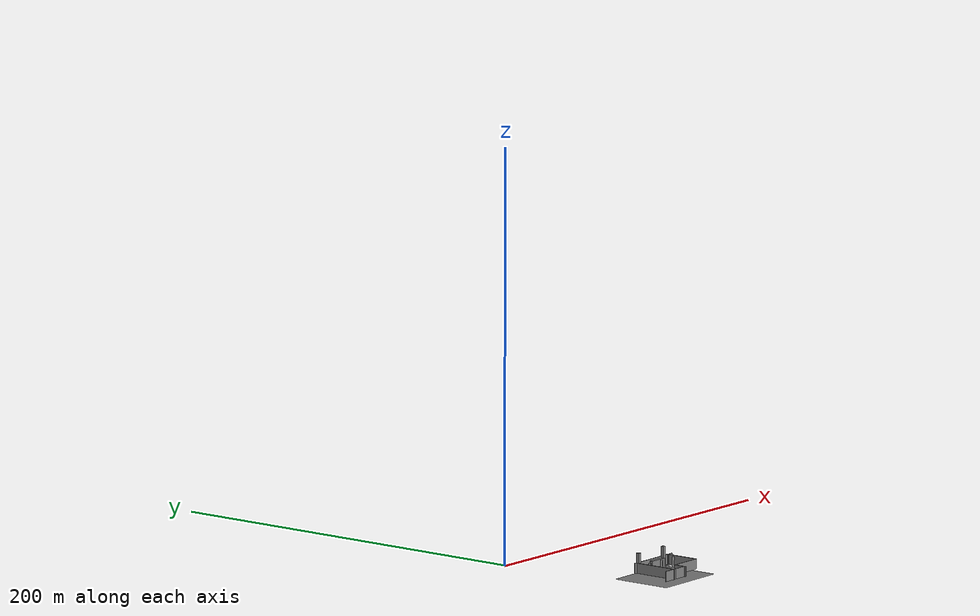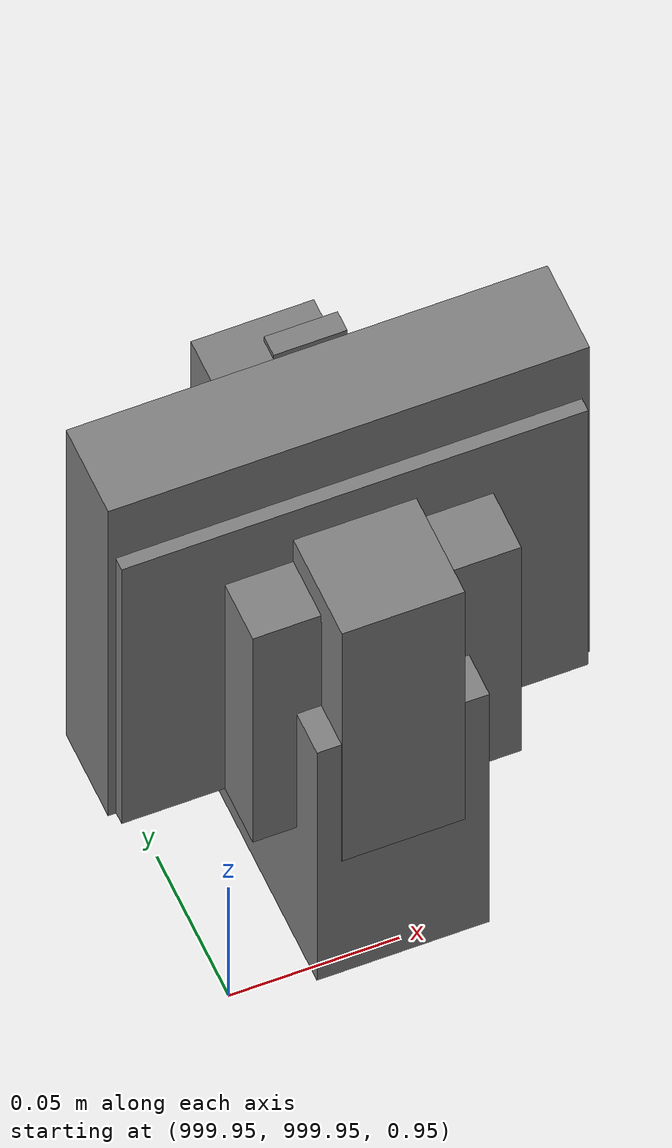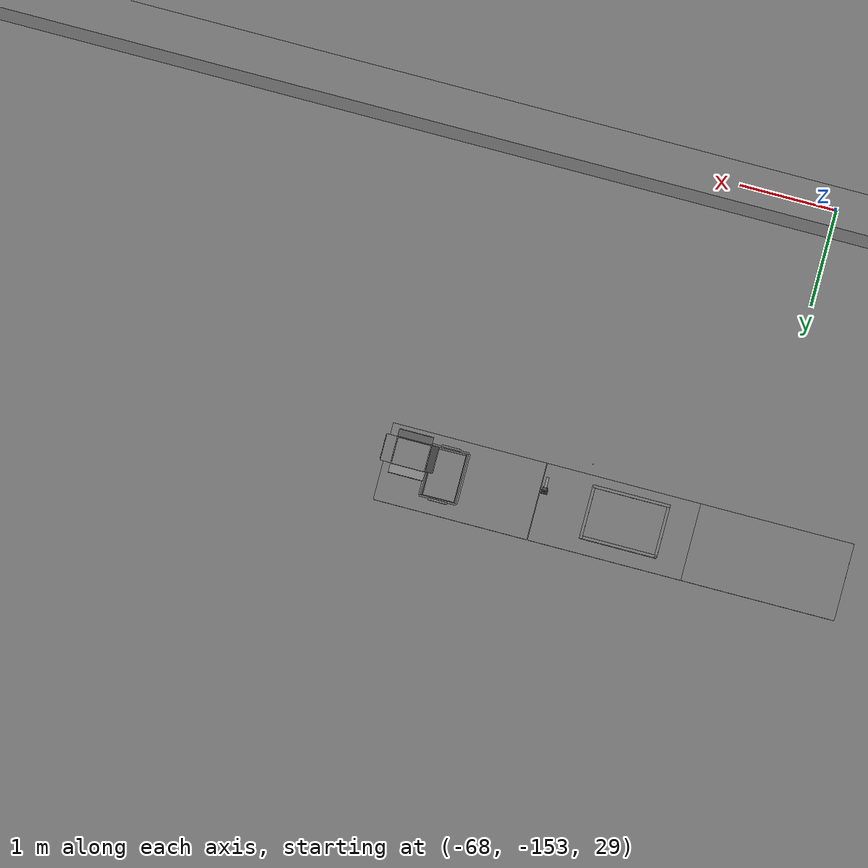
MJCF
<mujoco>
    <option gravity="0.000000000 0.000000000 -9.810000420" timestep="0.0049999999" integrator="implicitfast" density="1.225" viscosity="1.8000001e-05" noslip_iterations="10" iterations="100" sdf_iterations="50">
        <flag multiccd="disable"/>
    </option>
    <size memory="1000M"/>
    <compiler coordinate="local"/>
    <worldbody>
        <light cutoff="30" pos="0 1 1" dir="0 -1 -2"/>
        <light cutoff="30" pos="0 -1 1" dir="0 1 -2"/>
        <body pos="-64.866622925 -149.383972168 30.183746338" euler="89.999984741 89.999946594 0.000000000" name="openloong_gripper_2f85_fix_base_usda_bluebox_01">
            <geom contype="1" conaffinity="1" density="1000" type="box" material="" rgba="0.500000000 0.500000000 0.500000000 1.000000000" solimp="0.899999976 0.949999988 0.001000000" friction="1.000000000 0.005000000 0.000100000" solref="0.020000000 1.000000000" margin="0" condim="3" group="0" pos="0.276580811 0.187225342 0.000068665" quat="0.707106948 0.000077471 0.707106352 0.000077486" size="0.100000001 0.057999998 0.010000000" name="openloong_gripper_2f85_fix_base_usda_geom_B5233DC5_8D27_42C2_B630_82ECB3C67398"/>
            <geom contype="1" conaffinity="1" density="1000" type="box" material="" rgba="0.500000000 0.500000000 0.500000000 1.000000000" solimp="0.899999976 0.949999988 0.001000000" friction="1.000000000 0.005000000 0.000100000" solref="0.020000000 1.000000000" margin="0" condim="3" group="0" pos="0.000000000 0.002883911 0.000000000" quat="0.999999881 0.000000000 0.000000000 0.000000000" size="0.254000008 0.003000000 0.172000006" name="openloong_gripper_2f85_fix_base_usda_geom_033AB79C_97AA_48BC_AFCE_BF89E2FF6BF2"/>
            <geom contype="1" conaffinity="1" density="1000" type="box" material="" rgba="0.500000000 0.500000000 0.500000000 1.000000000" solimp="0.899999976 0.949999988 0.001000000" friction="1.000000000 0.005000000 0.000100000" solref="0.020000000 1.000000000" margin="0" condim="3" group="0" pos="0.000000000 0.124874115 0.173484802" quat="0.999796331 0.020176515 -0.000000015 0.000000030" size="0.259999990 0.119999997 0.007000000" name="openloong_gripper_2f85_fix_base_usda_geom_58537A6D_2B8E_403A_93D8_420F2A1288F4"/>
            <geom contype="1" conaffinity="1" density="1000" type="box" material="" rgba="0.500000000 0.500000000 0.500000000 1.000000000" solimp="0.899999976 0.949999988 0.001000000" friction="1.000000000 0.005000000 0.000100000" solref="0.020000000 1.000000000" margin="0" condim="3" group="0" pos="0.000000000 0.124874115 -0.173469543" quat="0.999796331 -0.020176545 -0.000000015 0.000000000" size="0.259999990 0.119999997 0.007000000" name="openloong_gripper_2f85_fix_base_usda_geom_E5DD0A40_A127_4209_A74B_51481DE057A7"/>
            <geom contype="1" conaffinity="1" density="1000" type="box" material="" rgba="0.500000000 0.500000000 0.500000000 1.000000000" solimp="0.899999976 0.949999988 0.001000000" friction="1.000000000 0.005000000 0.000100000" solref="0.020000000 1.000000000" margin="0" condim="3" group="0" pos="0.000000000 0.214008331 0.188980103" quat="0.999912977 0.013176724 0.000000015 0.000000000" size="0.259999990 0.029999999 0.012500000" name="openloong_gripper_2f85_fix_base_usda_geom_CC83872B_3FFA_474C_AABE_B90F0B508FA7"/>
            <geom contype="1" conaffinity="1" density="1000" type="box" material="" rgba="0.500000000 0.500000000 0.500000000 1.000000000" solimp="0.899999976 0.949999988 0.001000000" friction="1.000000000 0.005000000 0.000100000" solref="0.020000000 1.000000000" margin="0" condim="3" group="0" pos="-0.258361816 0.125289917 0.001876831" quat="0.702796936 -0.020792112 0.710783124 0.020769298" size="0.189999998 0.119999997 0.009000000" name="openloong_gripper_2f85_fix_base_usda_geom_29626615_1D13_48A6_91B7_B9034BF6F923"/>
            <geom contype="1" conaffinity="1" density="1000" type="box" material="" rgba="0.500000000 0.500000000 0.500000000 1.000000000" solimp="0.899999976 0.949999988 0.001000000" friction="1.000000000 0.005000000 0.000100000" solref="0.020000000 1.000000000" margin="0" condim="3" group="0" pos="0.000000000 0.214008331 -0.188980103" quat="0.999912977 -0.013176769 0.000000030 0.000000015" size="0.259999990 0.029999999 0.012500000" name="openloong_gripper_2f85_fix_base_usda_geom_7C8997A3_0BB0_4A4D_877F_23A1E82781E1"/>
            <geom contype="1" conaffinity="1" density="1000" type="box" material="" rgba="0.500000000 0.500000000 0.500000000 1.000000000" solimp="0.899999976 0.949999988 0.001000000" friction="1.000000000 0.005000000 0.000100000" solref="0.020000000 1.000000000" margin="0" condim="3" group="0" pos="-0.276611328 0.187225342 0.000068665" quat="0.707106650 0.000077441 0.707106709 0.000077456" size="0.100000001 0.057999998 0.010000000" name="openloong_gripper_2f85_fix_base_usda_geom_7346CEB7_2D95_42CE_91A3_5AA38348FDD1"/>
            <geom contype="1" conaffinity="1" density="1000" type="box" material="" rgba="0.500000000 0.500000000 0.500000000 1.000000000" solimp="0.899999976 0.949999988 0.001000000" friction="1.000000000 0.005000000 0.000100000" solref="0.020000000 1.000000000" margin="0" condim="3" group="0" pos="0.258331299 0.125289917 0.001876831" quat="0.702851415 0.018856421 0.710823774 -0.019329369" size="0.189999998 0.119999997 0.009000000" name="openloong_gripper_2f85_fix_base_usda_geom_8A5F6446_EF57_4EAE_93E2_20ADF5651249"/>
            <freejoint name="openloong_gripper_2f85_fix_base_usda_bluebox_01_joint"/>
            <site size="0.005000000 0.005000000 0.005000000" rgba="0.500000000 0.500000000 0.500000000 1.000000000" pos="0.000000000 0.000000000 0.000000000" quat="0.999961913 0.008726534 0.000000000 0.000000000" group="0" type="sphere" name="openloong_gripper_2f85_fix_base_usda_bluebox_01site"/>
        </body>
        <body pos="-64.496299744 -149.491867065 30.235729218" euler="0.000000000 0.000000000 89.999946594" name="openloong_gripper_2f85_fix_base_usda_cardboardbox_01">
            <geom contype="1" conaffinity="1" density="1000" type="box" material="" rgba="0.500000000 0.500000000 0.500000000 1.000000000" solimp="0.899999976 0.949999988 0.001000000" friction="1.000000000 0.005000000 0.000100000" solref="0.020000000 1.000000000" margin="0" condim="3" group="0" pos="-0.003166199 -0.004086494 0.005052090" quat="1.000000000 0.000000000 0.000000000 0.000000000" size="0.142499998 0.177500010 0.005000000" name="openloong_gripper_2f85_fix_base_usda_geom_E35A63E4_8FC5_4A24_A8DB_67230FB275D7"/>
            <geom contype="1" conaffinity="1" density="1000" type="box" material="" rgba="0.500000000 0.500000000 0.500000000 1.000000000" solimp="0.899999976 0.949999988 0.001000000" friction="1.000000000 0.005000000 0.000100000" solref="0.020000000 1.000000000" margin="0" condim="3" group="0" pos="-0.003166199 0.170316696 0.150570869" quat="1.000000000 0.000000000 0.000000000 0.000000000" size="0.142499998 0.005000000 0.149999991" name="openloong_gripper_2f85_fix_base_usda_geom_D9C72211_09C4_4D74_A6B5_DDCCF341F071"/>
            <geom contype="1" conaffinity="1" density="1000" type="box" material="" rgba="0.500000000 0.500000000 0.500000000 1.000000000" solimp="0.899999976 0.949999988 0.001000000" friction="1.000000000 0.005000000 0.000100000" solref="0.020000000 1.000000000" margin="0" condim="3" group="0" pos="-0.147399902 -0.005307198 0.150570869" quat="1.000000000 0.000000000 0.000000000 0.000000000" size="0.005000000 0.177500010 0.149999991" name="openloong_gripper_2f85_fix_base_usda_geom_B248CB7F_E11E_4810_8D4F_0252258DB267"/>
            <geom contype="1" conaffinity="1" density="1000" type="box" material="" rgba="0.500000000 0.500000000 0.500000000 1.000000000" solimp="0.899999976 0.949999988 0.001000000" friction="1.000000000 0.005000000 0.000100000" solref="0.020000000 1.000000000" margin="0" condim="3" group="0" pos="0.140275955 -0.005307198 0.150570869" quat="1.000000000 0.000000000 0.000000000 0.000000000" size="0.005000000 0.177500010 0.149999991" name="openloong_gripper_2f85_fix_base_usda_geom_0D0B0876_F8C6_4A0F_BD14_0EBB296CCE25"/>
            <geom contype="1" conaffinity="1" density="1000" type="box" material="" rgba="0.500000000 0.500000000 0.500000000 1.000000000" solimp="0.899999976 0.949999988 0.001000000" friction="1.000000000 0.005000000 0.000100000" solref="0.020000000 1.000000000" margin="0" condim="3" group="0" pos="-0.003166199 -0.181550980 0.150570869" quat="1.000000000 0.000000000 0.000000000 0.000000000" size="0.142499998 0.005000000 0.149999991" name="openloong_gripper_2f85_fix_base_usda_geom_CDF9D46C_08FE_421F_8282_05C85A31A82A"/>
            <freejoint name="openloong_gripper_2f85_fix_base_usda_cardboardbox_01_joint"/>
            <site size="0.005000000 0.005000000 0.005000000" rgba="0.500000000 0.500000000 0.500000000 1.000000000" pos="0.000000000 0.000000000 0.000000000" quat="0.999961913 0.008726535 0.000000000 0.000000000" group="0" type="sphere" name="openloong_gripper_2f85_fix_base_usda_site_5BB96A2D_D4DC_4328_A3E8_29421EB5E836"/>
            <body pos="0.139160156 -0.004048347 0.301930904" euler="-179.999954224 49.383502960 179.999954224" name="openloong_gripper_2f85_fix_base_usda_A1_006">
                <geom contype="1" conaffinity="1" density="1000" type="box" material="" rgba="0.500000000 0.500000000 0.500000000 1.000000000" solimp="0.899999976 0.949999988 0.001000000" friction="1.000000000 0.005000000 0.000100000" solref="0.020000000 1.000000000" margin="0" condim="3" group="0" pos="-0.071587563 0.000009537 0.001745224" quat="0.999999881 0.000000000 0.000000000 0.000000000" size="0.071249999 0.179999992 0.002500000" name="openloong_gripper_2f85_fix_base_usda_geom_AB22A9E4_62F5_4333_A869_2CA4B52712AC"/>
                <joint armature="0" stiffness="0.07" damping="0.0099999998" axis="0.000000 1.000000 0.000000" type="hinge" name="openloong_gripper_2f85_fix_base_usda_A1_006"/>
            </body>
            <body pos="-0.145902634 -0.004086494 0.301938057" euler="-180.000000000 -60.000011444 -180.000000000" name="openloong_gripper_2f85_fix_base_usda_A2_006">
                <geom contype="1" conaffinity="1" density="1000" type="box" material="" rgba="0.500000000 0.500000000 0.500000000 1.000000000" solimp="0.899999976 0.949999988 0.001000000" friction="1.000000000 0.005000000 0.000100000" solref="0.020000000 1.000000000" margin="0" condim="3" group="0" pos="0.071268082 0.000009537 0.002717972" quat="0.000002921 0.000000000 -0.000000030 0.999999881" size="0.071249999 0.179999992 0.002500000" name="openloong_gripper_2f85_fix_base_usda_geom_0FDA90F0_7569_4F2F_B1DD_9A910C5D7C3A"/>
                <joint armature="0" stiffness="0.07" damping="0.0099999998" axis="0.000000 1.000000 0.000000" type="hinge" name="openloong_gripper_2f85_fix_base_usda_A2_006"/>
            </body>
            <body pos="-0.003385544 0.175991058 0.301930904" euler="-125.858116150 -0.000004561 0.000002331" name="openloong_gripper_2f85_fix_base_usda_B2_006">
                <geom contype="1" conaffinity="1" density="1000" type="box" material="" rgba="0.500000000 0.500000000 0.500000000 1.000000000" solimp="0.899999976 0.949999988 0.001000000" friction="1.000000000 0.005000000 0.000100000" solref="0.020000000 1.000000000" margin="0" condim="3" group="0" pos="0.000009537 -0.070939064 -0.002470016" quat="0.999614120 0.027776197 -0.000000015 0.000000030" size="0.137500003 0.064999998 0.005000000" name="openloong_gripper_2f85_fix_base_usda_geom_61E64DDB_73FC_4E30_84DA_9AA529F67314"/>
                <joint armature="0" stiffness="0.07" damping="0.0099999998" axis="1.000000 0.000000 0.000000" type="hinge" name="openloong_gripper_2f85_fix_base_usda_B2_006"/>
            </body>
            <body pos="-0.003385544 -0.184140205 0.301938057" euler="147.805557251 0.000000000 0.000000000" name="openloong_gripper_2f85_fix_base_usda_B1_006">
                <geom contype="1" conaffinity="1" density="1000" type="box" material="" rgba="0.500000000 0.500000000 0.500000000 1.000000000" solimp="0.899999976 0.949999988 0.001000000" friction="1.000000000 0.005000000 0.000100000" solref="0.020000000 1.000000000" margin="0" condim="3" group="0" pos="-0.000028610 0.070202351 -0.002703667" quat="0.999614179 -0.027776167 0.000000000 0.000000000" size="0.137500003 0.064999998 0.005000000" name="openloong_gripper_2f85_fix_base_usda_geom_34789D73_9D30_47D9_8B4A_65E107163C69"/>
                <joint armature="0" stiffness="0.07" damping="0.0099999998" axis="1.000000 0.000000 0.000000" type="hinge" name="openloong_gripper_2f85_fix_base_usda_B1_006"/>
            </body>
        </body>
        <body pos="-65.882858276 -149.481979370 30.229999542" euler="-64.487716675 0.000000000 0.000000000" name="openloong_gripper_2f85_fix_base_usda_Barcode">
            <geom contype="1" conaffinity="1" density="1000" type="box" material="" rgba="0.500000000 0.500000000 0.500000000 1.000000000" solimp="0.899999976 0.949999988 0.001000000" friction="1.000000000 0.005000000 0.000100000" solref="0.020000000 1.000000000" margin="0" condim="3" group="0" pos="0.000000000 0.013038635 0.001419067" quat="0.000000000 0.000000000 0.000000000 1.000000119" size="0.034000002 0.010000000 0.017999999" name="openloong_gripper_2f85_fix_base_usda_geom_F7EDF6A0_6C77_4DF9_8F28_60D7A41AC201"/>
            <geom contype="1" conaffinity="1" density="1000" type="box" material="" rgba="0.500000000 0.500000000 0.500000000 1.000000000" solimp="0.899999976 0.949999988 0.001000000" friction="1.000000000 0.005000000 0.000100000" solref="0.020000000 1.000000000" margin="0" condim="3" group="0" pos="0.000000000 -0.035301208 -0.007095337" quat="0.000000000 0.000000000 -0.043619365 0.999048233" size="0.028999999 0.010000000 0.020000000" name="openloong_gripper_2f85_fix_base_usda_geom_0850D309_980F_481A_BC6B_A28852DE31E5"/>
            <geom contype="1" conaffinity="1" density="1000" type="box" material="" rgba="0.500000000 0.500000000 0.500000000 1.000000000" solimp="0.899999976 0.949999988 0.001000000" friction="1.000000000 0.005000000 0.000100000" solref="0.020000000 1.000000000" margin="0" condim="3" group="0" pos="0.000000000 -0.043411255 -0.011749268" quat="0.922262907 0.386563420 0.000000000 0.000000000" size="0.026000001 0.010000000 0.020000000" name="openloong_gripper_2f85_fix_base_usda_geom_C5556C6D_7253_4FE6_BFBE_4821A3262C54"/>
            <geom contype="1" conaffinity="1" density="1000" type="box" material="" rgba="0.500000000 0.500000000 0.500000000 1.000000000" solimp="0.899999976 0.949999988 0.001000000" friction="1.000000000 0.005000000 0.000100000" solref="0.020000000 1.000000000" margin="0" condim="3" group="0" pos="0.000000000 -0.016967773 -0.031860352" quat="0.000000000 0.000000000 0.000000000 1.000000119" size="0.008000000 0.010000000 0.013000000" name="openloong_gripper_2f85_fix_base_usda_geom_085A099A_E850_45BF_A342_92CF6F37CB08"/>
            <geom contype="1" conaffinity="1" density="1000" type="box" material="" rgba="0.500000000 0.500000000 0.500000000 1.000000000" solimp="0.899999976 0.949999988 0.001000000" friction="1.000000000 0.005000000 0.000100000" solref="0.020000000 1.000000000" margin="0" condim="3" group="0" pos="0.000000000 -0.001869202 0.000312805" quat="0.953716993 0.300705761 0.000000000 0.000000000" size="0.032000002 0.010000000 0.018999999" name="openloong_gripper_2f85_fix_base_usda_geom_1015B526_78F5_4DE2_8C8E_0272F4C1288C"/>
            <geom contype="1" conaffinity="1" density="1000" type="box" material="" rgba="0.500000000 0.500000000 0.500000000 1.000000000" solimp="0.899999976 0.949999988 0.001000000" friction="1.000000000 0.005000000 0.000100000" solref="0.020000000 1.000000000" margin="0" condim="3" group="0" pos="0.000000000 -0.019531250 -0.003173828" quat="0.953716993 0.300705761 0.000000000 0.000000000" size="0.030999999 0.010000000 0.020000000" name="openloong_gripper_2f85_fix_base_usda_geom_47D57275_8122_4BC0_8850_BCF49282CC36"/>
            <geom contype="1" conaffinity="1" density="1000" type="box" material="" rgba="0.500000000 0.500000000 0.500000000 1.000000000" solimp="0.899999976 0.949999988 0.001000000" friction="1.000000000 0.005000000 0.000100000" solref="0.020000000 1.000000000" margin="0" condim="3" group="0" pos="0.000000000 -0.035301208 -0.007095337" quat="0.953716993 0.300705761 0.000000000 0.000000000" size="0.028999999 0.010000000 0.020000000" name="openloong_gripper_2f85_fix_base_usda_geom_F5644FD5_1253_45C7_9630_B69D6A054F03"/>
            <geom contype="1" conaffinity="1" density="1000" type="box" material="" rgba="0.500000000 0.500000000 0.500000000 1.000000000" solimp="0.899999976 0.949999988 0.001000000" friction="1.000000000 0.005000000 0.000100000" solref="0.020000000 1.000000000" margin="0" condim="3" group="0" pos="0.000000000 -0.042617798 -0.071121216" quat="0.000000000 0.000000000 0.000000000 1.000000119" size="0.013000000 0.021000000 0.059999999" name="openloong_gripper_2f85_fix_base_usda_geom_C352DE6C_32C7_4AB5_A275_41BC293ACDBA"/>
            <freejoint name="openloong_gripper_2f85_fix_base_usda_Barcode_joint"/>
            <site size="0.005000000 0.005000000 0.005000000" rgba="0.500000000 0.500000000 0.500000000 1.000000000" pos="0.000000000 0.000000000 0.000000000" quat="1.000000000 0.000000000 0.000000000 0.000000000" group="0" type="sphere" name="openloong_gripper_2f85_fix_base_usda_Barcode_site"/>
        </body>
        <body pos="-66.745018005 -149.392349243 30.184000015" euler="0.000000000 0.000000000 89.999946594" name="[22332900005085]_Basket_01">
            <geom contype="1" conaffinity="1" density="1000" type="box" material="" rgba="0.500000000 0.500000000 0.500000000 1.000000000" solimp="0.899999976 0.949999988 0.001000000" friction="1.000000000 0.005000000 0.000100000" solref="0.020000000 1.000000000" margin="0" condim="3" group="0" pos="-0.052425385 0.389207840 0.089787483" quat="0.707107008 0.000000000 0.000000000 0.707106411" size="0.014249999 0.014249999 0.059999999" name="[22332900005085]_geom_503143A7_3127_4E49_A799_28E126065DFF"/>
            <geom contype="1" conaffinity="1" density="1000" type="box" material="" rgba="0.500000000 0.500000000 0.500000000 1.000000000" solimp="0.899999976 0.949999988 0.001000000" friction="1.000000000 0.005000000 0.000100000" solref="0.020000000 1.000000000" margin="0" condim="3" group="0" pos="0.264015198 -0.133043289 0.089787483" quat="0.707107008 0.000000000 0.000000000 0.707106411" size="0.014249999 0.014249999 0.059999999" name="[22332900005085]_geom_782A60F0_ACA8_4B0F_8C6F_649C942F4C83"/>
            <geom contype="1" conaffinity="1" density="1000" type="box" material="" rgba="0.500000000 0.500000000 0.500000000 1.000000000" solimp="0.899999976 0.949999988 0.001000000" friction="1.000000000 0.005000000 0.000100000" solref="0.020000000 1.000000000" margin="0" condim="3" group="0" pos="-0.264015198 -0.265548706 0.089793205" quat="0.707107008 0.000000000 0.000000000 0.707106411" size="0.014249999 0.014249999 0.059999999" name="[22332900005085]_geom_354B8475_CECF_4E90_A839_375E96E0C2BE"/>
            <geom contype="1" conaffinity="1" density="1000" type="box" material="" rgba="0.500000000 0.500000000 0.500000000 1.000000000" solimp="0.899999976 0.949999988 0.001000000" friction="1.000000000 0.005000000 0.000100000" solref="0.020000000 1.000000000" margin="0" condim="3" group="0" pos="-0.160263062 -0.389322281 0.089793205" quat="0.707107008 0.000000000 0.000000000 0.707106411" size="0.014249999 0.014249999 0.059999999" name="[22332900005085]_geom_3F68120E_76AB_45ED_8F45_3392573F2B9F"/>
            <geom contype="1" conaffinity="1" density="1000" type="box" material="" rgba="0.500000000 0.500000000 0.500000000 1.000000000" solimp="0.899999976 0.949999988 0.001000000" friction="1.000000000 0.005000000 0.000100000" solref="0.020000000 1.000000000" margin="0" condim="3" group="0" pos="0.162265778 -0.389322281 0.089787483" quat="0.707107008 0.000000000 0.000000000 0.707106411" size="0.014249999 0.014249999 0.059999999" name="[22332900005085]_geom_2F420AC2_1165_4113_B26A_D11C0ECD34C9"/>
            <geom contype="1" conaffinity="1" density="1000" type="box" material="" rgba="0.500000000 0.500000000 0.500000000 1.000000000" solimp="0.899999976 0.949999988 0.001000000" friction="1.000000000 0.005000000 0.000100000" solref="0.020000000 1.000000000" margin="0" condim="3" group="0" pos="0.264015198 0.389207840 0.089787483" quat="0.707107008 0.000000000 0.000000000 0.707106411" size="0.014249999 0.014249999 0.059999999" name="[22332900005085]_geom_02CD81AC_B8A5_484F_BBAE_684899A0DA7A"/>
            <geom contype="1" conaffinity="1" density="1000" type="box" material="" rgba="0.500000000 0.500000000 0.500000000 1.000000000" solimp="0.899999976 0.949999988 0.001000000" friction="1.000000000 0.005000000 0.000100000" solref="0.020000000 1.000000000" margin="0" condim="3" group="0" pos="-0.264015198 -0.133043289 0.089793205" quat="0.707107008 0.000000000 0.000000000 0.707106411" size="0.014249999 0.014249999 0.059999999" name="[22332900005085]_geom_396464CE_26B8_4DAB_B1BC_BC5B1179F0DD"/>
            <geom contype="1" conaffinity="1" density="1000" type="box" material="" rgba="0.500000000 0.500000000 0.500000000 1.000000000" solimp="0.899999976 0.949999988 0.001000000" friction="1.000000000 0.005000000 0.000100000" solref="0.020000000 1.000000000" margin="0" condim="3" group="0" pos="-0.264026642 0.269256592 0.089793205" quat="0.707107008 0.000000000 0.000000000 0.707106411" size="0.014249999 0.014249999 0.059999999" name="[22332900005085]_geom_12F2F2DB_87E9_43F7_8BEC_B304386FA43E"/>
            <geom contype="1" conaffinity="1" density="1000" type="box" material="" rgba="0.500000000 0.500000000 0.500000000 1.000000000" solimp="0.899999976 0.949999988 0.001000000" friction="1.000000000 0.005000000 0.000100000" solref="0.020000000 1.000000000" margin="0" condim="3" group="0" pos="0.054462433 0.389207840 0.089787483" quat="0.707107008 0.000000000 0.000000000 0.707106411" size="0.014249999 0.014249999 0.059999999" name="[22332900005085]_geom_4437A809_5B0D_40B7_8801_B7CC630FECEC"/>
            <geom contype="1" conaffinity="1" density="1000" type="box" material="" rgba="0.500000000 0.500000000 0.500000000 1.000000000" solimp="0.899999976 0.949999988 0.001000000" friction="1.000000000 0.005000000 0.000100000" solref="0.020000000 1.000000000" margin="0" condim="3" group="0" pos="0.054462433 -0.389322281 0.089787483" quat="0.707107008 0.000000000 0.000000000 0.707106411" size="0.014249999 0.014249999 0.059999999" name="[22332900005085]_geom_1B5B0152_9FBB_4318_90F9_B2B3F07AA392"/>
            <geom contype="1" conaffinity="1" density="1000" type="box" material="" rgba="0.500000000 0.500000000 0.500000000 1.000000000" solimp="0.899999976 0.949999988 0.001000000" friction="1.000000000 0.005000000 0.000100000" solref="0.020000000 1.000000000" margin="0" condim="3" group="0" pos="0.264015198 0.269256592 0.089793205" quat="0.707107008 0.000000000 0.000000000 0.707106411" size="0.014249999 0.014249999 0.059999999" name="[22332900005085]_geom_C7B5307C_06D0_4427_A843_825AC4D4F97E"/>
            <geom contype="1" conaffinity="1" density="1000" type="box" material="" rgba="0.500000000 0.500000000 0.500000000 1.000000000" solimp="0.899999976 0.949999988 0.001000000" friction="1.000000000 0.005000000 0.000100000" solref="0.020000000 1.000000000" margin="0" condim="3" group="0" pos="0.264015198 -0.389322281 0.089787483" quat="0.707107008 0.000000000 0.000000000 0.707106411" size="0.014249999 0.014249999 0.059999999" name="[22332900005085]_geom_36438C96_CEF2_4433_ADFC_6D4618824FA1"/>
            <geom contype="1" conaffinity="1" density="1000" type="box" material="" rgba="0.500000000 0.500000000 0.500000000 1.000000000" solimp="0.899999976 0.949999988 0.001000000" friction="1.000000000 0.005000000 0.000100000" solref="0.020000000 1.000000000" margin="0" condim="3" group="0" pos="0.000000000 0.000000000 0.015998840" quat="0.707107008 0.000000000 0.000000000 0.707106411" size="0.403499991 0.279000014 0.015750000" name="[22332900005085]_geom_CCAB8EDD_148C_4022_9072_C0A5E767D1DA"/>
            <geom contype="1" conaffinity="1" density="1000" type="box" material="" rgba="0.500000000 0.500000000 0.500000000 1.000000000" solimp="0.899999976 0.949999988 0.001000000" friction="1.000000000 0.005000000 0.000100000" solref="0.020000000 1.000000000" margin="0" condim="3" group="0" pos="0.000000000 -0.389476776 0.163619041" quat="0.707107008 0.000000000 0.000000000 0.707106411" size="0.015000000 0.277500004 0.015750000" name="[22332900005085]_geom_F1683A81_637A_4394_863D_004F050E5CC9"/>
            <geom contype="1" conaffinity="1" density="1000" type="box" material="" rgba="0.500000000 0.500000000 0.500000000 1.000000000" solimp="0.899999976 0.949999988 0.001000000" friction="1.000000000 0.005000000 0.000100000" solref="0.020000000 1.000000000" margin="0" condim="3" group="0" pos="0.162265778 0.389207840 0.089787483" quat="0.707107008 0.000000000 0.000000000 0.707106411" size="0.014249999 0.014249999 0.059999999" name="[22332900005085]_geom_2B1CBC99_2DBC_4D4E_9B68_DB89BA36EA66"/>
            <geom contype="1" conaffinity="1" density="1000" type="box" material="" rgba="0.500000000 0.500000000 0.500000000 1.000000000" solimp="0.899999976 0.949999988 0.001000000" friction="1.000000000 0.005000000 0.000100000" solref="0.020000000 1.000000000" margin="0" condim="3" group="0" pos="0.000000000 0.389471054 0.163619041" quat="0.707107008 0.000000000 0.000000000 0.707106411" size="0.015000000 0.277500004 0.015750000" name="[22332900005085]_geom_62D809B4_72EA_4160_B1B0_5EBF49039AB7"/>
            <geom contype="1" conaffinity="1" density="1000" type="box" material="" rgba="0.500000000 0.500000000 0.500000000 1.000000000" solimp="0.899999976 0.949999988 0.001000000" friction="1.000000000 0.005000000 0.000100000" solref="0.020000000 1.000000000" margin="0" condim="3" group="0" pos="-0.263511658 0.000000000 0.163619041" quat="0.707107008 0.000000000 0.000000000 0.707106411" size="0.403499991 0.015000000 0.015750000" name="[22332900005085]_geom_E7C9AAEB_80DE_4207_8B88_79BA0F3BAC98"/>
            <geom contype="1" conaffinity="1" density="1000" type="box" material="" rgba="0.500000000 0.500000000 0.500000000 1.000000000" solimp="0.899999976 0.949999988 0.001000000" friction="1.000000000 0.005000000 0.000100000" solref="0.020000000 1.000000000" margin="0" condim="3" group="0" pos="-0.264015198 0.141334534 0.089793205" quat="0.707107008 0.000000000 0.000000000 0.707106411" size="0.014249999 0.014249999 0.059999999" name="[22332900005085]_geom_EF335AAA_4F22_4841_B45C_91A7BA3403AC"/>
            <geom contype="1" conaffinity="1" density="1000" type="box" material="" rgba="0.500000000 0.500000000 0.500000000 1.000000000" solimp="0.899999976 0.949999988 0.001000000" friction="1.000000000 0.005000000 0.000100000" solref="0.020000000 1.000000000" margin="0" condim="3" group="0" pos="0.264015198 -0.265548706 0.089787483" quat="0.707107008 0.000000000 0.000000000 0.707106411" size="0.014249999 0.014249999 0.059999999" name="[22332900005085]_geom_20E9A4C4_BACA_4333_80BA_7462FDC92CA0"/>
            <geom contype="1" conaffinity="1" density="1000" type="box" material="" rgba="0.500000000 0.500000000 0.500000000 1.000000000" solimp="0.899999976 0.949999988 0.001000000" friction="1.000000000 0.005000000 0.000100000" solref="0.020000000 1.000000000" margin="0" condim="3" group="0" pos="-0.160263062 0.389207840 0.089787483" quat="0.707107008 0.000000000 0.000000000 0.707106411" size="0.014249999 0.014249999 0.059999999" name="[22332900005085]_geom_2D8EF99A_72E8_4683_9B8C_6A0B643A8A95"/>
            <geom contype="1" conaffinity="1" density="1000" type="box" material="" rgba="0.500000000 0.500000000 0.500000000 1.000000000" solimp="0.899999976 0.949999988 0.001000000" friction="1.000000000 0.005000000 0.000100000" solref="0.020000000 1.000000000" margin="0" condim="3" group="0" pos="-0.052425385 -0.389322281 0.089787483" quat="0.707107008 0.000000000 0.000000000 0.707106411" size="0.014249999 0.014249999 0.059999999" name="[22332900005085]_geom_952D8FE6_B2F4_4E1E_87F8_E61709A9FEB1"/>
            <geom contype="1" conaffinity="1" density="1000" type="box" material="" rgba="0.500000000 0.500000000 0.500000000 1.000000000" solimp="0.899999976 0.949999988 0.001000000" friction="1.000000000 0.005000000 0.000100000" solref="0.020000000 1.000000000" margin="0" condim="3" group="0" pos="-0.264026642 -0.389322281 0.089793205" quat="0.707107008 0.000000000 0.000000000 0.707106411" size="0.014249999 0.014249999 0.059999999" name="[22332900005085]_geom_8F276570_99E0_4F34_BF61_E523D3C2F727"/>
            <geom contype="1" conaffinity="1" density="1000" type="box" material="" rgba="0.500000000 0.500000000 0.500000000 1.000000000" solimp="0.899999976 0.949999988 0.001000000" friction="1.000000000 0.005000000 0.000100000" solref="0.020000000 1.000000000" margin="0" condim="3" group="0" pos="0.264015198 0.141334534 0.089787483" quat="0.707107008 0.000000000 0.000000000 0.707106411" size="0.014249999 0.014249999 0.059999999" name="[22332900005085]_geom_1556E536_FD01_4F49_A5BC_B4470E07CA42"/>
            <geom contype="1" conaffinity="1" density="1000" type="box" material="" rgba="0.500000000 0.500000000 0.500000000 1.000000000" solimp="0.899999976 0.949999988 0.001000000" friction="1.000000000 0.005000000 0.000100000" solref="0.020000000 1.000000000" margin="0" condim="3" group="0" pos="-0.264015198 0.389207840 0.089793205" quat="0.707107008 0.000000000 0.000000000 0.707106411" size="0.014249999 0.014249999 0.059999999" name="[22332900005085]_geom_CC6C500C_5E85_4F3D_9080_8402694AE7D7"/>
            <geom contype="1" conaffinity="1" density="1000" type="box" material="" rgba="0.500000000 0.500000000 0.500000000 1.000000000" solimp="0.899999976 0.949999988 0.001000000" friction="1.000000000 0.005000000 0.000100000" solref="0.020000000 1.000000000" margin="0" condim="3" group="0" pos="0.264015198 0.004480362 0.089787483" quat="0.707107008 0.000000000 0.000000000 0.707106411" size="0.014249999 0.014249999 0.059999999" name="[22332900005085]_geom_6B187EEE_BB25_4953_86FE_D7156A96F315"/>
            <geom contype="1" conaffinity="1" density="1000" type="box" material="" rgba="0.500000000 0.500000000 0.500000000 1.000000000" solimp="0.899999976 0.949999988 0.001000000" friction="1.000000000 0.005000000 0.000100000" solref="0.020000000 1.000000000" margin="0" condim="3" group="0" pos="0.263694763 -0.000011444 0.163619041" quat="0.707107008 0.000000000 0.000000000 0.707106411" size="0.403499991 0.015000000 0.015750000" name="[22332900005085]_geom_C13CBBF4_EB73_4517_B513_B6919594DE3F"/>
            <geom contype="1" conaffinity="1" density="1000" type="box" material="" rgba="0.500000000 0.500000000 0.500000000 1.000000000" solimp="0.899999976 0.949999988 0.001000000" friction="1.000000000 0.005000000 0.000100000" solref="0.020000000 1.000000000" margin="0" condim="3" group="0" pos="-0.264015198 0.004480362 0.089793205" quat="0.707107008 0.000000000 0.000000000 0.707106411" size="0.014249999 0.014249999 0.059999999" name="[22332900005085]_geom_94E0E96F_FBED_4938_A41B_655EF57E2D48"/>
            <freejoint name="[22332900005085]_joint_E7083E26_39E6_4667_B1BB_A8F902431164"/>
        </body>
        <body pos="0.000000000 0.000000000 0.000000000" euler="0.000000000 0.000000000 0.000000000" name="Static Objects_Static Objects">
            <geom contype="1" conaffinity="1" density="1000" type="box" material="" rgba="0.500000000 0.500000000 0.500000000 1.000000000" solimp="0.899999976 0.949999988 0.001000000" friction="1.000000000 0.005000000 0.000100000" solref="0.020000000 1.000000000" margin="0" condim="3" group="0" pos="-67.544113159 -149.365814209 29.727830887" quat="0.500000417 0.499999970 0.499999553 0.499999970" size="0.381000012 0.319999993 0.041000001" name="Static Objects_geom_A2F1AB9C_5067_4E8A_AF0E_CC7EABDD34CF"/>
            <geom contype="1" conaffinity="1" density="1000" type="box" material="" rgba="0.500000000 0.500000000 0.500000000 1.000000000" solimp="0.899999976 0.949999988 0.001000000" friction="1.000000000 0.005000000 0.000100000" solref="0.020000000 1.000000000" margin="0" condim="3" group="0" pos="-68.239501953 -149.365814209 30.086868286" quat="0.500000417 0.499999970 0.499999553 0.499999970" size="0.370999992 0.039500002 0.745000005" name="Static Objects_geom_351E58DF_3C7C_4602_9A66_ABB9459ED955"/>
            <geom contype="1" conaffinity="1" density="1000" type="box" material="" rgba="0.500000000 0.500000000 0.500000000 1.000000000" solimp="0.899999976 0.949999988 0.001000000" friction="1.000000000 0.005000000 0.000100000" solref="0.020000000 1.000000000" margin="0" condim="3" group="0" pos="-68.239501953 -149.365814209 30.147235870" quat="0.500000417 0.499999970 0.499999553 0.499999970" size="0.400000006 0.022000000 0.800000012" name="Static Objects_geom_3CE98DFF_5A9E_4BA7_8458_4BE2ADFAB650"/>
            <geom contype="1" conaffinity="1" density="1000" type="box" material="" rgba="0.500000000 0.500000000 0.500000000 1.000000000" solimp="0.899999976 0.949999988 0.001000000" friction="1.000000000 0.005000000 0.000100000" solref="0.020000000 1.000000000" margin="0" condim="3" group="0" pos="-68.934890747 -149.365814209 29.727830887" quat="0.500000417 0.499999970 0.499999553 0.499999970" size="0.381000012 0.319999993 0.041000001" name="Static Objects_geom_84560998_9705_4606_9B49_09B899E71D22"/>
            <geom contype="1" conaffinity="1" density="1000" type="box" material="" rgba="0.500000000 0.500000000 0.500000000 1.000000000" solimp="0.899999976 0.949999988 0.001000000" friction="1.000000000 0.005000000 0.000100000" solref="0.020000000 1.000000000" margin="0" condim="3" group="0" pos="-68.239501953 -149.365814209 29.561563492" quat="0.500000417 0.499999970 0.499999553 0.499999970" size="0.020000000 0.022000000 0.660000026" name="Static Objects_geom_11AD76B9_999B_47EF_A1FC_3FF4AD5CCE82"/>
            <geom contype="1" conaffinity="1" density="1000" type="box" material="" rgba="0.500000000 0.500000000 0.500000000 1.000000000" solimp="0.899999976 0.949999988 0.001000000" friction="1.000000000 0.005000000 0.000100000" solref="0.020000000 1.000000000" margin="0" condim="3" group="0" pos="-65.945671082 -149.365814209 29.727830887" quat="0.500000417 0.499999970 0.499999553 0.499999970" size="0.381000012 0.319999993 0.041000001" name="Static Objects_geom_2C1D8D2A_E2AA_4CB2_BA3A_3577ABA5D826"/>
            <geom contype="1" conaffinity="1" density="1000" type="box" material="" rgba="0.500000000 0.500000000 0.500000000 1.000000000" solimp="0.899999976 0.949999988 0.001000000" friction="1.000000000 0.005000000 0.000100000" solref="0.020000000 1.000000000" margin="0" condim="3" group="0" pos="-66.641059875 -149.365814209 30.086868286" quat="0.500000417 0.499999970 0.499999553 0.499999970" size="0.370999992 0.039500002 0.745000005" name="Static Objects_geom_E8B897A7_AD63_4F18_96F4_98F34B4413AC"/>
            <geom contype="1" conaffinity="1" density="1000" type="box" material="" rgba="0.500000000 0.500000000 0.500000000 1.000000000" solimp="0.899999976 0.949999988 0.001000000" friction="1.000000000 0.005000000 0.000100000" solref="0.020000000 1.000000000" margin="0" condim="3" group="0" pos="-66.641059875 -149.365814209 30.147235870" quat="0.500000417 0.499999970 0.499999553 0.499999970" size="0.400000006 0.022000000 0.800000012" name="Static Objects_geom_C44FC95F_467A_4497_AA85_5D5A3EC7DA5F"/>
            <geom contype="1" conaffinity="1" density="1000" type="box" material="" rgba="0.500000000 0.500000000 0.500000000 1.000000000" solimp="0.899999976 0.949999988 0.001000000" friction="1.000000000 0.005000000 0.000100000" solref="0.020000000 1.000000000" margin="0" condim="3" group="0" pos="-67.336448669 -149.365814209 29.727830887" quat="0.500000417 0.499999970 0.499999553 0.499999970" size="0.381000012 0.319999993 0.041000001" name="Static Objects_geom_4DD6411E_C6A2_4CAE_ACF7_768A93D97002"/>
            <geom contype="1" conaffinity="1" density="1000" type="box" material="" rgba="0.500000000 0.500000000 0.500000000 1.000000000" solimp="0.899999976 0.949999988 0.001000000" friction="1.000000000 0.005000000 0.000100000" solref="0.020000000 1.000000000" margin="0" condim="3" group="0" pos="-66.641059875 -149.365814209 29.561563492" quat="0.500000417 0.499999970 0.499999553 0.499999970" size="0.020000000 0.022000000 0.660000026" name="Static Objects_geom_944D7DF8_A6C0_489B_BD2A_7C5B839CA3DF"/>
            <geom contype="1" conaffinity="1" density="1000" type="box" material="" rgba="0.500000000 0.500000000 0.500000000 1.000000000" solimp="0.899999976 0.949999988 0.001000000" friction="1.000000000 0.005000000 0.000100000" solref="0.020000000 1.000000000" margin="0" condim="3" group="0" pos="-64.338577271 -149.365814209 29.727830887" quat="0.500000417 0.499999970 0.499999553 0.499999970" size="0.381000012 0.319999993 0.041000001" name="Static Objects_geom_47170528_42AA_4141_8C42_1AF14D1413A2"/>
            <geom contype="1" conaffinity="1" density="1000" type="box" material="" rgba="0.500000000 0.500000000 0.500000000 1.000000000" solimp="0.899999976 0.949999988 0.001000000" friction="1.000000000 0.005000000 0.000100000" solref="0.020000000 1.000000000" margin="0" condim="3" group="0" pos="-65.033966064 -149.365814209 30.086868286" quat="0.500000417 0.499999970 0.499999553 0.499999970" size="0.370999992 0.039500002 0.745000005" name="Static Objects_geom_AEBD3D66_1EC8_4F63_A207_C7F2660EBEE3"/>
            <geom contype="1" conaffinity="1" density="1000" type="box" material="" rgba="0.500000000 0.500000000 0.500000000 1.000000000" solimp="0.899999976 0.949999988 0.001000000" friction="1.000000000 0.005000000 0.000100000" solref="0.020000000 1.000000000" margin="0" condim="3" group="0" pos="-65.033966064 -149.365814209 30.147235870" quat="0.500000417 0.499999970 0.499999553 0.499999970" size="0.400000006 0.022000000 0.800000012" name="Static Objects_geom_086EB85A_C04D_46AC_AF06_04BBB11B3486"/>
            <geom contype="1" conaffinity="1" density="1000" type="box" material="" rgba="0.500000000 0.500000000 0.500000000 1.000000000" solimp="0.899999976 0.949999988 0.001000000" friction="1.000000000 0.005000000 0.000100000" solref="0.020000000 1.000000000" margin="0" condim="3" group="0" pos="-65.729354858 -149.365814209 29.727830887" quat="0.500000417 0.499999970 0.499999553 0.499999970" size="0.381000012 0.319999993 0.041000001" name="Static Objects_geom_3D73A8C4_375B_4C2F_A203_44BC8CA026D9"/>
            <geom contype="1" conaffinity="1" density="1000" type="box" material="" rgba="0.500000000 0.500000000 0.500000000 1.000000000" solimp="0.899999976 0.949999988 0.001000000" friction="1.000000000 0.005000000 0.000100000" solref="0.020000000 1.000000000" margin="0" condim="3" group="0" pos="-65.033966064 -149.365814209 29.561563492" quat="0.500000417 0.499999970 0.499999553 0.499999970" size="0.020000000 0.022000000 0.660000026" name="Static Objects_geom_9EE97CD2_D3CF_45F0_8600_E607B4855776"/>
            <geom contype="1" conaffinity="1" density="1000" type="box" material="" rgba="0.500000000 0.500000000 0.500000000 1.000000000" solimp="0.899999976 0.949999988 0.001000000" friction="1.000000000 0.005000000 0.000100000" solref="0.020000000 1.000000000" margin="0" condim="3" group="0" pos="-61.754566193 -137.853729248 33.906845093" quat="0.707107067 0.000000000 0.000000000 0.707106471" size="0.759999990 0.759999990 4.500000000" name="Static Objects_geom_9BDF2A51_4945_40C9_8FF8_7B05FC2429BF"/>
            <geom contype="1" conaffinity="1" density="1000" type="box" material="" rgba="0.500000000 0.500000000 0.500000000 1.000000000" solimp="0.899999976 0.949999988 0.001000000" friction="1.000000000 0.005000000 0.000100000" solref="0.020000000 1.000000000" margin="0" condim="3" group="0" pos="-57.511135101 -144.927108765 31.707921982" quat="1.000000000 0.000000000 0.000000000 0.000000000" size="0.200000003 8.000000000 2.299999952" name="Static Objects_geom_0094DED3_A449_4CFC_8785_F01FEB898FBD"/>
            <geom contype="1" conaffinity="1" density="1000" type="box" material="" rgba="0.500000000 0.500000000 0.500000000 1.000000000" solimp="0.899999976 0.949999988 0.001000000" friction="1.000000000 0.005000000 0.000100000" solref="0.020000000 1.000000000" margin="0" condim="3" group="0" pos="-80.517646790 -157.574050903 31.688196182" quat="0.707107067 0.000000000 0.000000000 0.707106471" size="0.600000024 0.600000024 2.299999952" name="Static Objects_geom_1EDEEEBF_4405_4D48_B254_E3CD73F9983E"/>
            <geom contype="1" conaffinity="1" density="1000" type="box" material="" rgba="0.500000000 0.500000000 0.500000000 1.000000000" solimp="0.899999976 0.949999988 0.001000000" friction="1.000000000 0.005000000 0.000100000" solref="0.020000000 1.000000000" margin="0" condim="3" group="0" pos="-80.711044312 -147.414932251 31.666158676" quat="1.000000000 0.000000000 0.000000000 0.000000000" size="0.200000003 10.000000000 2.299999952" name="Static Objects_geom_3992820A_AD24_4583_A992_37D66B24E4F0"/>
            <geom contype="1" conaffinity="1" density="1000" type="box" material="" rgba="0.500000000 0.500000000 0.500000000 1.000000000" solimp="0.899999976 0.949999988 0.001000000" friction="1.000000000 0.005000000 0.000100000" solref="0.020000000 1.000000000" margin="0" condim="3" group="0" pos="-57.687217712 -137.434692383 31.688196182" quat="0.707107067 0.000000000 0.000000000 0.707106471" size="0.600000024 0.600000024 2.299999952" name="Static Objects_geom_7758CB09_5F22_494A_9BF3_9DD02EA198E5"/>
            <geom contype="1" conaffinity="1" density="1000" type="box" material="" rgba="0.500000000 0.500000000 0.500000000 1.000000000" solimp="0.899999976 0.949999988 0.001000000" friction="1.000000000 0.005000000 0.000100000" solref="0.020000000 1.000000000" margin="0" condim="3" group="0" pos="-69.537033081 -140.263229370 31.714921951" quat="0.707107067 0.000000000 0.000000000 0.707106471" size="0.759999990 4.500000000 2.299999952" name="Static Objects_geom_A95121A8_A0B1_40C2_ADB2_A0B9BA040705"/>
            <geom contype="1" conaffinity="1" density="1000" type="box" material="" rgba="0.500000000 0.500000000 0.500000000 1.000000000" solimp="0.899999976 0.949999988 0.001000000" friction="1.000000000 0.005000000 0.000100000" solref="0.020000000 1.000000000" margin="0" condim="3" group="0" pos="-80.073638916 -137.853713989 33.906845093" quat="0.707107067 0.000000000 0.000000000 0.707106471" size="0.759999990 0.759999990 4.500000000" name="Static Objects_geom_6D184804_B2B9_429F_87B2_2F94DBC3B250"/>
            <geom contype="1" conaffinity="1" density="1000" type="box" material="" rgba="0.500000000 0.500000000 0.500000000 1.000000000" solimp="0.899999976 0.949999988 0.001000000" friction="1.000000000 0.005000000 0.000100000" solref="0.020000000 1.000000000" margin="0" condim="3" group="0" pos="-73.406707764 -155.734664917 31.707921982" quat="1.000000000 0.000000000 0.000000000 0.000000000" size="0.200000003 3.000000000 2.299999952" name="Static Objects_geom_36307A5F_8DFD_4B8E_A44D_3D6318234E79"/>
            <geom contype="1" conaffinity="1" density="1000" type="box" material="" rgba="0.500000000 0.500000000 0.500000000 1.000000000" solimp="0.899999976 0.949999988 0.001000000" friction="1.000000000 0.005000000 0.000100000" solref="0.020000000 1.000000000" margin="0" condim="3" group="0" pos="-68.497543335 -137.448257446 31.707921982" quat="0.707107067 0.000000000 0.000000000 0.707106471" size="0.200000003 14.000000000 2.299999952" name="Static Objects_geom_B58FE6C0_646D_4598_8F7C_C407DCAB1550"/>
            <geom contype="1" conaffinity="1" density="1000" type="cylinder" material="" rgba="0.500000000 0.500000000 0.500000000 1.000000000" solimp="0.899999976 0.949999988 0.001000000" friction="1.000000000 0.005000000 0.000100000" solref="0.020000000 1.000000000" margin="0" condim="3" group="0" pos="-68.868522644 -142.134506226 31.711090088" quat="0.707107067 0.000000000 0.000000000 0.707106471" size="0.509999990 2.299999952 1.000000000" name="Static Objects_geom_E9CE8EF7_E3BF_4F23_9253_462E13753299"/>
            <geom contype="1" conaffinity="1" density="1000" type="plane" material="" rgba="0.500000000 0.500000000 0.500000000 1.000000000" solimp="0.899999976 0.949999988 0.001000000" friction="1.000000000 0.005000000 0.000100000" solref="0.020000000 1.000000000" margin="0" condim="3" group="0" pos="-72.873703003 -147.131927490 29.409669876" quat="1.000000000 0.000000000 0.000000000 0.000000000" size="18.000000000 14.000000000 1.000000000" name="Static Objects_geom_E25E3722_0158_45CB_97BE_DEDB61CE4889"/>
            <geom contype="1" conaffinity="1" density="1000" type="box" material="" rgba="0.500000000 0.500000000 0.500000000 1.000000000" solimp="0.899999976 0.949999988 0.001000000" friction="1.000000000 0.005000000 0.000100000" solref="0.020000000 1.000000000" margin="0" condim="3" group="0" pos="-79.943580627 -157.782272339 31.707921982" quat="0.707107067 0.000000000 0.000000000 0.707106471" size="0.200000003 7.000000000 2.299999952" name="Static Objects_geom_D9A6DEA8_F783_49B5_A28D_6B13F9CA6710"/>
            <geom contype="1" conaffinity="1" density="1000" type="box" material="" rgba="0.500000000 0.500000000 0.500000000 1.000000000" solimp="0.899999976 0.949999988 0.001000000" friction="1.000000000 0.005000000 0.000100000" solref="0.020000000 1.000000000" margin="0" condim="3" group="0" pos="-65.421028137 -152.903442383 31.707921982" quat="0.707107067 0.000000000 0.000000000 0.707106471" size="0.200000003 7.800000191 2.299999952" name="Static Objects_geom_83592BD0_8FFE_4F23_961B_DFDB370C3624"/>
            <geom contype="1" conaffinity="1" density="1000" type="box" material="" rgba="0.500000000 0.500000000 0.500000000 1.000000000" solimp="0.899999976 0.949999988 0.001000000" friction="1.000000000 0.005000000 0.000100000" solref="0.020000000 1.000000000" margin="0" condim="3" group="0" pos="-74.776908875 -149.964416504 31.688196182" quat="1.000000000 0.000000000 0.000000000 0.000000000" size="0.600000024 0.409999996 2.299999952" name="Static Objects_geom_EAED0278_8EAD_4A90_BA43_3EDD5A4429A2"/>
            <geom contype="1" conaffinity="1" density="1000" type="cylinder" material="" rgba="0.500000000 0.500000000 0.500000000 1.000000000" solimp="0.899999976 0.949999988 0.001000000" friction="1.000000000 0.005000000 0.000100000" solref="0.020000000 1.000000000" margin="0" condim="3" group="0" pos="-60.161884308 -142.134506226 31.711090088" quat="0.707107067 0.000000000 0.000000000 0.707106471" size="0.509999990 2.299999952 1.000000000" name="Static Objects_geom_1A78DFF6_BD50_43F9_9B2F_6D3A6B2FAF38"/>
            <geom contype="1" conaffinity="1" density="1000" type="cylinder" material="" rgba="0.500000000 0.500000000 0.500000000 1.000000000" solimp="0.899999976 0.949999988 0.001000000" friction="1.000000000 0.005000000 0.000100000" solref="0.020000000 1.000000000" margin="0" condim="3" group="0" pos="-75.382453918 -149.963455200 31.711090088" quat="0.707107067 0.000000000 0.000000000 0.707106471" size="0.409999996 2.299999952 1.000000000" name="Static Objects_geom_CDD9F399_2F6B_4EB8_8CC9_038B53106512"/>
            <geom contype="1" conaffinity="1" density="1000" type="cylinder" material="" rgba="0.500000000 0.500000000 0.500000000 1.000000000" solimp="0.899999976 0.949999988 0.001000000" friction="1.000000000 0.005000000 0.000100000" solref="0.020000000 1.000000000" margin="0" condim="3" group="0" pos="-74.154960632 -149.963455200 31.711090088" quat="0.707107067 0.000000000 0.000000000 0.707106471" size="0.409999996 2.299999952 1.000000000" name="Static Objects_geom_344248D1_26BB_4D6E_A95D_0D394B2DFEF9"/>
            <geom contype="1" conaffinity="1" density="1000" type="cylinder" material="" rgba="0.500000000 0.500000000 0.500000000 1.000000000" solimp="0.899999976 0.949999988 0.001000000" friction="1.000000000 0.005000000 0.000100000" solref="0.020000000 1.000000000" margin="0" condim="3" group="0" pos="-77.566612244 -142.134506226 31.711090088" quat="0.707107067 0.000000000 0.000000000 0.707106471" size="0.509999990 2.299999952 1.000000000" name="Static Objects_geom_6F1D48D0_B991_464F_A6E6_773F3F7DCD46"/>
        </body>
        <body pos="1000.000000000 1000.000000000 1.000000000" euler="0.000000000 0.000000000 180.000000000" name="openloong_gripper_2f85_fix_base_usda_battery_01">
            <geom contype="1" conaffinity="1" density="1000" type="box" material="" rgba="0.500000000 0.500000000 0.500000000 1.000000000" solimp="0.899999976 0.949999988 0.001000000" friction="1.000000000 0.005000000 0.000100000" solref="0.020000000 1.000000000" margin="0" condim="3" group="0" pos="-0.011123657 -0.041940309 0.101691343" quat="1.000000000 0.000000000 0.000000000 0.000000000" size="0.010800000 0.003375000 0.004725000" name="openloong_gripper_2f85_fix_base_usda_geom_7D3D726F_21E5_4235_9B05_E37F70B6B927"/>
            <geom contype="1" conaffinity="1" density="1000" type="box" material="" rgba="0.500000000 0.500000000 0.500000000 1.000000000" solimp="0.899999976 0.949999988 0.001000000" friction="1.000000000 0.005000000 0.000100000" solref="0.020000000 1.000000000" margin="0" condim="3" group="0" pos="-0.010876465 -0.044247437 0.047066893" quat="0.998702705 -0.050920475 0.000000000 0.000000000" size="0.009450001 0.002700000 0.024975000" name="openloong_gripper_2f85_fix_base_usda_geom_40DED804_DD66_480A_8EA8_B8D23DC3A9D5"/>
            <geom contype="1" conaffinity="1" density="1000" type="box" material="" rgba="0.500000000 0.500000000 0.500000000 1.000000000" solimp="0.899999976 0.949999988 0.001000000" friction="1.000000000 0.005000000 0.000100000" solref="0.020000000 1.000000000" margin="0" condim="3" group="0" pos="-0.001235962 -0.000659180 0.047381196" quat="1.000000000 0.000000000 0.000000000 0.000000000" size="0.039420001 0.039150000 0.047250003" name="openloong_gripper_2f85_fix_base_usda_geom_45DD82E9_7CA5_4769_9914_B39C6EF0337C"/>
            <geom contype="1" conaffinity="1" density="1000" type="box" material="" rgba="0.500000000 0.500000000 0.500000000 1.000000000" solimp="0.899999976 0.949999988 0.001000000" friction="1.000000000 0.005000000 0.000100000" solref="0.020000000 1.000000000" margin="0" condim="3" group="0" pos="-0.010876465 -0.039138794 0.009851727" quat="1.000000000 0.000000000 0.000000000 0.000000000" size="0.009450001 0.010800000 0.013500000" name="openloong_gripper_2f85_fix_base_usda_geom_24845EE6_06DC_4CF8_980F_7927E316E564"/>
            <geom contype="1" conaffinity="1" density="1000" type="box" material="" rgba="0.500000000 0.500000000 0.500000000 1.000000000" solimp="0.899999976 0.949999988 0.001000000" friction="1.000000000 0.005000000 0.000100000" solref="0.020000000 1.000000000" margin="0" condim="3" group="0" pos="-0.010876465 -0.041528322 0.071508206" quat="1.000000000 0.000000000 0.000000000 0.000000000" size="0.009450001 0.002700000 0.027000001" name="openloong_gripper_2f85_fix_base_usda_geom_7BEBD4E9_8FDC_4324_8A55_776D8167F214"/>
            <freejoint name="openloong_gripper_2f85_fix_base_usda_battery_01_joint"/>
            <site size="0.005000000 0.005000000 0.005000000" rgba="0.500000000 0.500000000 0.500000000 1.000000000" pos="0.000000000 0.000000000 0.000000000" quat="0.999961913 0.008726500 0.000000000 0.000000000" group="0" type="sphere" name="openloong_gripper_2f85_fix_base_usda_battery_01site"/>
        </body>
        <body pos="-65.842971802 -148.925674438 31.164009094" euler="-111.830635071 69.812217712 -30.249778748" mocap="true" name="spotlight5_SpotLight"/>
        <body pos="1000.000000000 1000.000000000 1.000000000" euler="0.000011953 0.000005123 -179.999984741" name="openloong_gripper_2f85_fix_base_usda_intel_box">
            <geom contype="1" conaffinity="1" density="1000" type="box" material="" rgba="0.500000000 0.500000000 0.500000000 1.000000000" solimp="0.899999976 0.949999988 0.001000000" friction="1.000000000 0.005000000 0.000100000" solref="0.020000000 1.000000000" margin="0" condim="3" group="0" pos="0.000000000 -0.000067139 0.000082284" quat="0.707106709 0.000000225 0.000000253 0.707106650" size="0.052800003 0.025300000 0.052800003" name="openloong_gripper_2f85_fix_base_usda_geom_8EC56F01_CA84_40B9_B918_58CBE32AC0DC"/>
            <freejoint name="openloong_gripper_2f85_fix_base_usda_intel_box_joint"/>
            <site size="0.005000000 0.005000000 0.005000000" rgba="0.500000000 0.500000000 0.500000000 1.000000000" pos="0.000000000 0.000000000 0.000000000" quat="0.999961913 0.008726500 0.000000000 0.000000000" group="0" type="sphere" name="openloong_gripper_2f85_fix_base_usda_intel_boxsite"/>
        </body>
        <body pos="-65.810142517 -149.077789307 31.162294388" euler="116.460700989 28.152654648 39.499713898" mocap="true" name="spotlight3_SpotLight"/>
        <body pos="1000.000000000 1000.000000000 1.000000000" euler="0.000000000 0.000000000 180.000000000" name="openloong_gripper_2f85_fix_base_usda_cpu_fan">
            <geom contype="1" conaffinity="1" density="1000" type="box" material="" rgba="0.500000000 0.500000000 0.500000000 1.000000000" solimp="0.899999976 0.949999988 0.001000000" friction="1.000000000 0.005000000 0.000100000" solref="0.020000000 1.000000000" margin="0" condim="3" group="0" pos="0.000000000 0.000000000 0.070034981" quat="0.000000000 0.000000000 0.000000000 1.000000000" size="0.070700005 0.014699999 0.070700005" name="openloong_gripper_2f85_fix_base_usda_geom_07CA8A7D_355C_4619_8741_08CBDF39213C"/>
            <freejoint name="openloong_gripper_2f85_fix_base_usda_cpu_fan_joint"/>
            <site size="0.005000000 0.005000000 0.005000000" rgba="0.500000000 0.500000000 0.500000000 1.000000000" pos="0.000000000 0.000000000 0.000000000" quat="0.999961913 0.008726535 0.000000000 0.000000000" group="0" type="sphere" name="openloong_gripper_2f85_fix_base_usda_cpu_fancsite"/>
        </body>
        <body pos="1000.000000000 1000.000000000 1.000000000" euler="0.000000000 0.000000000 180.000000000" name="openloong_gripper_2f85_fix_base_usda_wifi_box">
            <geom contype="1" conaffinity="1" density="1000" type="box" material="" rgba="0.500000000 0.500000000 0.500000000 1.000000000" solimp="0.899999976 0.949999988 0.001000000" friction="1.000000000 0.005000000 0.000100000" solref="0.020000000 1.000000000" margin="0" condim="3" group="0" pos="0.000000000 0.000000000 0.058978677" quat="0.000000000 0.000000047 0.000000000 1.000000000" size="0.068499997 0.018999999 0.059000000" name="openloong_gripper_2f85_fix_base_usda_geom_4CCF7AF9_C171_433C_AC0B_F9E36E417AF9"/>
            <freejoint name="openloong_gripper_2f85_fix_base_usda_wifi_box_joint"/>
            <site size="0.005000000 0.005000000 0.005000000" rgba="0.500000000 0.500000000 0.500000000 1.000000000" pos="0.000000000 0.000000000 0.000000000" quat="0.999961913 0.008726500 0.000000000 0.000000000" group="0" type="sphere" name="openloong_gripper_2f85_fix_base_usda_wifi_boxsite"/>
        </body>
        <body pos="1000.000000000 999.999938965 1.000000000" euler="0.000000000 0.000000000 180.000000000" name="openloong_gripper_2f85_fix_base_usda_intelcore_i5">
            <geom contype="1" conaffinity="1" density="1000" type="box" material="" rgba="0.500000000 0.500000000 0.500000000 1.000000000" solimp="0.899999976 0.949999988 0.001000000" friction="1.000000000 0.005000000 0.000100000" solref="0.020000000 1.000000000" margin="0" condim="3" group="0" pos="0.000000000 0.000000000 0.051722717" quat="0.707106709 0.000000000 0.000000000 -0.707106769" size="0.052800000 0.018080002 0.052800000" name="openloong_gripper_2f85_fix_base_usda_geom_38E552C2_70AF_45B8_962A_162E7EB9B427"/>
            <freejoint name="openloong_gripper_2f85_fix_base_usda_intelcore_i5_joint"/>
            <site size="0.005000000 0.005000000 0.005000000" rgba="0.500000000 0.500000000 0.500000000 1.000000000" pos="0.000000000 0.000000000 0.000000000" quat="0.999961913 0.008726534 0.000000000 0.000000000" group="0" type="sphere" name="openloong_gripper_2f85_fix_base_usda_intelcore_i5site"/>
        </body>
        <body pos="-66.033996582 -148.925689697 31.169239044" euler="-0.951802075 51.454963684 102.485313416" mocap="true" name="spotlight2_SpotLight"/>
        <body pos="-66.291030884 -149.869689941 29.018842697" euler="0.000000000 0.000000000 89.999946594" mocap="true" name="openloong_gripper_2f85_fix_base_usda_leftHandMocap"/>
        <body pos="-66.291030884 -149.869689941 29.018842697" euler="0.000000000 0.000000000 89.999946594" mocap="true" name="openloong_gripper_2f85_fix_base_usda_rightHandMocap"/>
        <body pos="-66.291030884 -149.869689941 30.218843460" euler="0.000000000 0.000000000 89.999946594" name="openloong_gripper_2f85_fix_base_usda_base_link">
            <geom contype="1" conaffinity="1" density="1000" type="mesh" material="" rgba="0.783999979 0.783999979 0.783999979 1.000000000" solimp="0.899999976 0.949999988 0.001000000" friction="1.000000000 0.005000000 0.000100000" solref="0.020000000 1.000000000" margin="0" condim="3" group="3" mesh="base_link" pos="0.000000000 0.000000000 0.000000000" quat="1.000000000 0.000000000 0.000000000 0.000000000" size="1.000000000 1.000000000 1.000000000" name="openloong_gripper_2f85_fix_base_usda__geom_7_1BFDD3C3_B6E9_4409_87F1_4A8919CD6E1C"/>
            <site size="0.005000000 0.005000000 0.005000000" rgba="0.500000000 0.500000000 0.500000000 1.000000000" pos="0.000000000 0.000000000 0.000000000" quat="1.000000000 0.000000000 0.000000000 0.000000000" group="0" type="sphere" name="openloong_gripper_2f85_fix_base_usda_imu"/>
            <inertial mass="22.447001" pos="-0.005664100 -0.001336700 0.238289997" diaginertia="0.374352545 0.277180195 0.220617250" quat="0.999247074 0.035235517 -0.015086859 0.006023135"/>
            <body pos="0.000000000 0.000000000 0.299997330" euler="0.000000000 0.000000000 0.000000000" name="openloong_gripper_2f85_fix_base_usda_dummy_body">
                <geom contype="1" conaffinity="1" density="1000" type="sphere" material="" rgba="0.783999979 0.783999979 0.783999979 1.000000000" solimp="0.899999976 0.949999988 0.001000000" friction="1.000000000 0.005000000 0.000100000" solref="0.020000000 1.000000000" margin="0" condim="3" group="3" pos="0.000000000 0.000000000 0.000000000" quat="1.000000000 0.000000000 0.000000000 0.000000000" size="0.010000000 0.000000000 0.000000000" name="openloong_gripper_2f85_fix_base_usda__geom_8_D73F7E54_33D9_4641_952F_9612659C8BCE"/>
                <joint armature="0.0099999998" stiffness="0" damping="0.1" axis="0.000000 0.000000 1.000000" type="hinge" name="openloong_gripper_2f85_fix_base_usda_dummy_joint"/>
                <site size="0.010000000 0.005000000 0.005000000" rgba="0.500000000 0.500000000 0.500000000 1.000000000" pos="0.000000000 0.000000000 0.000000000" quat="1.000000000 0.000000000 0.000000000 0.000000000" group="3" type="sphere" name="openloong_gripper_2f85_fix_base_usda_dummy_site"/>
            </body>
            <body pos="0.009002686 0.000000000 0.406400681" euler="0.000000000 0.000000000 0.000000000" name="openloong_gripper_2f85_fix_base_usda_Link_head_yaw">
                <geom contype="1" conaffinity="1" density="1000" type="mesh" material="" rgba="0.783999979 0.783999979 0.783999979 1.000000000" solimp="0.899999976 0.949999988 0.001000000" friction="1.000000000 0.005000000 0.000100000" solref="0.020000000 1.000000000" margin="0" condim="3" group="3" mesh="Link_head_yaw" pos="0.000000000 0.000000000 0.000000000" quat="1.000000000 0.000000000 0.000000000 0.000000000" size="1.000000000 1.000000000 1.000000000" name="openloong_gripper_2f85_fix_base_usda__geom_10_25E4C757_C549_4C37_8D12_885C39D7FE16"/>
                <inertial mass="0.84249002" pos="0.000000000 -0.002081400 0.044801001" diaginertia="0.000700588 0.000629000 0.000553812" quat="0.706933022 -0.015675601 0.015677100 0.706933022"/>
                <body pos="0.000000000 -0.034599304 0.048500061" euler="0.000000000 0.000000000 0.000000000" name="openloong_gripper_2f85_fix_base_usda_Link_head_pitch">
                    <geom contype="1" conaffinity="1" density="1000" type="mesh" material="" rgba="0.783999979 0.783999979 0.783999979 1.000000000" solimp="0.899999976 0.949999988 0.001000000" friction="1.000000000 0.005000000 0.000100000" solref="0.020000000 1.000000000" margin="0" condim="3" group="3" mesh="Link_head_pitch" pos="0.000000000 0.000000000 0.000000000" quat="1.000000000 0.000000000 0.000000000 0.000000000" size="1.000000000 1.000000000 1.000000000" name="openloong_gripper_2f85_fix_base_usda__geom_12_DE39FAAF_E3A3_4E74_BA9F_61CD029C913D"/>
                    <inertial mass="1.3943" pos="0.020569000 0.033004001 0.125000000" diaginertia="0.006381400 0.006289940 0.004481460" quat="0.973390222 0.008406822 0.228157058 0.019624906"/>
                    <body pos="0.000000000 0.029998779 0.000000000" euler="0.000000000 0.000000000 0.000000000" name="openloong_gripper_2f85_fix_base_usda_neck_center_body">
                        <site size="0.010000000 0.005000000 0.005000000" rgba="0.500000000 0.500000000 0.500000000 1.000000000" pos="0.000000000 0.000000000 0.000000000" quat="1.000000000 0.000000000 0.000000000 0.000000000" group="3" type="sphere" name="openloong_gripper_2f85_fix_base_usda_neck_center_site"/>
                        <body pos="0.020004272 0.000000000 0.149999619" euler="-0.000002229 39.998176575 -90.000205994" name="openloong_gripper_2f85_fix_base_usda_camera_head">
                            <site size="0.010000000 0.005000000 0.005000000" rgba="0.500000000 0.500000000 0.500000000 1.000000000" pos="0.000000000 0.000000000 0.000000000" quat="1.000000000 0.000000000 0.000000000 0.000000000" group="3" type="sphere" name="openloong_gripper_2f85_fix_base_usda_camera_head_site"/>
                        </body>
                    </body>
                </body>
            </body>
            <body pos="0.003997803 -0.161598206 0.392200470" euler="0.000000000 0.000000000 0.000000000" name="openloong_gripper_2f85_fix_base_usda_Link_arm_r_01">
                <geom contype="1" conaffinity="1" density="1000" type="mesh" material="" rgba="0.783999979 0.783999979 0.783999979 1.000000000" solimp="0.899999976 0.949999988 0.001000000" friction="1.000000000 0.005000000 0.000100000" solref="0.020000000 1.000000000" margin="0" condim="3" group="3" mesh="Link_arm_r_01" pos="0.000000000 0.000000000 0.000000000" quat="1.000000000 0.000000000 0.000000000 0.000000000" size="1.000000000 1.000000000 1.000000000" name="openloong_gripper_2f85_fix_base_usda__geom_14_ECC77509_1D70_4774_A5DC_BEE1C03A3AD9"/>
                <joint armature="0.0099999998" stiffness="0" damping="1" axis="0.000000 -1.000000 0.000000" limited="true" range="-170.000015259 170.000015259" type="hinge" name="openloong_gripper_2f85_fix_base_usda_J_arm_r_01"/>
                <inertial mass="0.75641" pos="0.004494600 -0.038293999 -0.000001874" diaginertia="0.000842990 0.000803050 0.000587120" quat="-0.000163502 0.707098067 0.000812463 0.707115054"/>
                <body pos="-0.041992188 -0.041000366 0.000000000" euler="0.000000000 0.000000000 0.000000000" name="openloong_gripper_2f85_fix_base_usda_Link_arm_r_02">
                    <geom contype="1" conaffinity="1" density="1000" type="mesh" material="" rgba="0.783999979 0.783999979 0.783999979 1.000000000" solimp="0.899999976 0.949999988 0.001000000" friction="1.000000000 0.005000000 0.000100000" solref="0.020000000 1.000000000" margin="0" condim="3" group="3" mesh="Link_arm_r_02" pos="0.000000000 0.000000000 0.000000000" quat="1.000000000 0.000000000 0.000000000 0.000000000" size="1.000000000 1.000000000 1.000000000" name="openloong_gripper_2f85_fix_base_usda__geom_16_A02B8751_36EC_4077_B8D7_4A9F58B54328"/>
                    <joint armature="0.0099999998" stiffness="0" damping="1" axis="-1.000000 0.000000 0.000000" limited="true" range="-105.000244141 105.000244141" type="hinge" name="openloong_gripper_2f85_fix_base_usda_J_arm_r_02"/>
                    <inertial mass="0.98500001" pos="0.041999999 -0.067430697 0.000000000" diaginertia="0.002262690 0.001730990 0.001154020" quat="0.500000000 0.500000000 -0.500000000 0.500000000"/>
                    <body pos="0.041992188 -0.122596741 0.000000000" euler="0.000000000 0.000000000 0.000000000" name="openloong_gripper_2f85_fix_base_usda_Link_arm_r_03">
                        <geom contype="1" conaffinity="1" density="1000" type="mesh" material="" rgba="0.783999979 0.783999979 0.783999979 1.000000000" solimp="0.899999976 0.949999988 0.001000000" friction="1.000000000 0.005000000 0.000100000" solref="0.020000000 1.000000000" margin="0" condim="3" group="3" mesh="Link_arm_r_03" pos="0.000000000 0.000000000 0.000000000" quat="1.000000000 0.000000000 0.000000000 0.000000000" size="1.000000000 1.000000000 1.000000000" name="openloong_gripper_2f85_fix_base_usda__geom_18_44FA8C1D_53AF_4197_A366_FA511A655449"/>
                        <joint armature="0.0099999998" stiffness="0" damping="1" axis="0.000000 -1.000000 0.000000" limited="true" range="-170.000015259 170.000015259" type="hinge" name="openloong_gripper_2f85_fix_base_usda_J_arm_r_03"/>
                        <inertial mass="0.95899999" pos="-0.001413580 -0.164663002 0.020757901" diaginertia="0.002101340 0.002064590 0.000754802" quat="0.560480952 0.454391927 -0.443732947 0.531497955"/>
                        <body pos="0.035293579 -0.177406311 0.023998260" euler="0.000000000 0.000000000 0.000000000" name="openloong_gripper_2f85_fix_base_usda_Link_arm_r_04">
                            <geom contype="1" conaffinity="1" density="1000" type="mesh" material="" rgba="0.783999979 0.783999979 0.783999979 1.000000000" solimp="0.899999976 0.949999988 0.001000000" friction="1.000000000 0.005000000 0.000100000" solref="0.020000000 1.000000000" margin="0" condim="3" group="3" mesh="Link_arm_r_04" pos="0.000000000 0.000000000 0.000000000" quat="1.000000000 0.000000000 0.000000000 0.000000000" size="1.000000000 1.000000000 1.000000000" name="openloong_gripper_2f85_fix_base_usda__geom_20_70394443_4AFB_4103_9808_2E851903B953"/>
                            <joint armature="0.0099999998" stiffness="0" damping="1" axis="-1.000000 0.000000 0.000000" limited="true" range="0.000000000 170.000015259" type="hinge" name="openloong_gripper_2f85_fix_base_usda_J_arm_r_04"/>
                            <inertial mass="0.60000002" pos="-0.038727000 -0.060766999 -0.021003000" diaginertia="0.001092610 0.000712422 0.000645102" quat="0.327701002 0.632602990 -0.467366993 0.523443997"/>
                            <body pos="-0.035293579 -0.103492737 -0.023998260" euler="0.000000000 0.000000000 0.000000000" name="openloong_gripper_2f85_fix_base_usda_Link_arm_r_05">
                                <geom contype="1" conaffinity="1" density="1000" type="mesh" material="" rgba="0.783999979 0.783999979 0.783999979 1.000000000" solimp="0.899999976 0.949999988 0.001000000" friction="1.000000000 0.005000000 0.000100000" solref="0.020000000 1.000000000" margin="0" condim="3" group="3" mesh="Link_arm_r_05" pos="0.000000000 0.000000000 0.000000000" quat="1.000000000 0.000000000 0.000000000 0.000000000" size="1.000000000 1.000000000 1.000000000" name="openloong_gripper_2f85_fix_base_usda__geom_22_F240B003_5F09_4538_BD3E_63777FA43BFD"/>
                                <joint armature="0.0099999998" stiffness="0" damping="1" axis="0.000000 -1.000000 0.000000" limited="true" range="-170.000015259 170.000015259" type="hinge" name="openloong_gripper_2f85_fix_base_usda_J_arm_r_05"/>
                                <inertial mass="0.68976003" pos="0.000032712 -0.068658002 -0.000111780" diaginertia="0.002522510 0.002411100 0.000448695" quat="0.707660973 0.706543028 -0.002603360 0.002470550"/>
                                <body pos="-0.026489258 -0.196502686 0.000000000" euler="0.000000000 0.000000000 0.000000000" name="openloong_gripper_2f85_fix_base_usda_Link_arm_r_06">
                                    <geom contype="1" conaffinity="1" density="1000" type="mesh" material="" rgba="0.783999979 0.783999979 0.783999979 1.000000000" solimp="0.899999976 0.949999988 0.001000000" friction="1.000000000 0.005000000 0.000100000" solref="0.020000000 1.000000000" margin="0" condim="3" group="3" mesh="Link_arm_r_06" pos="0.000000000 0.000000000 0.000000000" quat="1.000000000 0.000000000 0.000000000 0.000000000" size="1.000000000 1.000000000 1.000000000" name="openloong_gripper_2f85_fix_base_usda__geom_24_49A23645_690C_4FCD_9F83_A38AD796739E"/>
                                    <joint armature="0.0099999998" stiffness="0" damping="1" axis="1.000000 0.000000 0.000000" limited="true" range="-105.000244141 105.000244141" type="hinge" name="openloong_gripper_2f85_fix_base_usda_J_arm_r_06"/>
                                    <inertial mass="0.28" pos="0.026078001 -0.000000896 0.001663700" diaginertia="0.000156930 0.000145601 0.000104979" quat="0.707080841 0.001851080 0.001883810 0.707127810"/>
                                    <body pos="0.026489258 0.000000000 0.031799316" euler="0.000000000 0.000000000 0.000000000" name="openloong_gripper_2f85_fix_base_usda_Link_arm_r_07">
                                        <geom contype="1" conaffinity="1" density="1000" type="mesh" material="" rgba="0.783999979 0.783999979 0.783999979 1.000000000" solimp="0.899999976 0.949999988 0.001000000" friction="1.000000000 0.005000000 0.000100000" solref="0.020000000 1.000000000" margin="0" condim="3" group="3" mesh="Link_arm_r_07" pos="0.000000000 0.000000000 0.000000000" quat="1.000000000 0.000000000 0.000000000 0.000000000" size="1.000000000 1.000000000 1.000000000" name="openloong_gripper_2f85_fix_base_usda__geom_26_C4264390_0737_4B2E_BB22_52D6E9DD3391"/>
                                        <joint armature="0.0099999998" stiffness="0" damping="1" axis="0.000000 0.000000 1.000000" limited="true" range="-60.000133514 60.000133514" type="hinge" name="openloong_gripper_2f85_fix_base_usda_J_arm_r_07"/>
                                        <inertial mass="0.61353999" pos="-0.007859000 -0.158170000 -0.027736001" diaginertia="0.003037610 0.002570910 0.000729379" quat="0.427542925 0.443532884 -0.553093910 0.560867906"/>
                                        <body pos="0.000000000 0.286994934 -0.270000458" euler="150.000350952 -0.000001649 -0.000000442" name="openloong_gripper_2f85_fix_base_usda_camera_wrist_r">
                                            <site size="0.010000000 0.005000000 0.005000000" rgba="0.500000000 0.500000000 0.500000000 1.000000000" pos="0.000000000 0.000000000 0.000000000" quat="1.000000000 0.000000000 0.000000000 0.000000000" group="3" type="sphere" name="openloong_gripper_2f85_fix_base_usda_camera_wrist_r_site"/>
                                        </body>
                                        <body pos="0.000000000 -0.220008850 -0.033002853" euler="0.000000000 0.000000000 179.999969482" name="openloong_gripper_2f85_fix_base_usda_ee_center_body_r">
                                            <site size="0.010000000 0.005000000 0.005000000" rgba="0.500000000 0.500000000 0.500000000 1.000000000" pos="0.000000000 0.000000000 0.000000000" quat="1.000000000 0.000000000 0.000000000 0.000000000" group="3" type="sphere" name="openloong_gripper_2f85_fix_base_usda_ee_center_site_r"/>
                                        </body>
                                        <body pos="0.000000000 -0.066001892 -0.031000137" euler="89.999984741 0.000000000 180.000000000" name="openloong_gripper_2f85_fix_base_usda_zbr_base_link">
                                            <geom contype="1" conaffinity="1" density="1000" type="mesh" material="" rgba="0.783999979 0.783999979 0.783999979 1.000000000" solimp="0.899999976 0.949999988 0.001000000" friction="1.000000000 0.005000000 0.000100000" solref="0.020000000 1.000000000" margin="0" condim="3" group="3" mesh="base" pos="0.000000000 0.000003815 -0.000007629" quat="1.000000000 0.000000000 0.000000000 0.000000000" size="1.000000238 1.000000238 1.000000238" name="openloong_gripper_2f85_fix_base_usda__geom_30_603E7B57_E090_4C90_B3FF_E7D54410915E"/>
                                            <inertial mass="0.77744102" pos="0.000000000 -0.000027039 0.035467502" diaginertia="0.000260285 0.000225381 0.000152708" quat="0.999998808 -0.001528488 0.000000000 0.000000000"/>
                                            <body pos="-0.030609138 0.004745484 0.065696731" euler="-89.999984741 -0.000000000 0.000000000" name="openloong_gripper_2f85_fix_base_usda_r_left_driver">
                                                <geom contype="1" conaffinity="1" density="1000" type="mesh" material="" rgba="0.783999979 0.783999979 0.783999979 1.000000000" solimp="0.899999976 0.949999988 0.001000000" friction="1.000000000 0.005000000 0.000100000" solref="0.020000000 1.000000000" margin="0" condim="3" group="3" mesh="driver" pos="0.030609138 0.054901138 -0.004699708" quat="0.707106829 0.707106709 0.000000000 -0.000000000" size="1.000000238 1.000000238 1.000000238" name="openloong_gripper_2f85_fix_base_usda__geom_32_199A7B12_65E3_496F_87AC_F3C9042BCFB1"/>
                                                <joint armature="0.0049999999" stiffness="0" damping="0.1" axis="0.000000 0.000000 1.000000" limited="true" range="0.000000000 51.566200256" type="hinge" name="openloong_gripper_2f85_fix_base_usda_r_left_driver_joint"/>
                                                <inertial mass="0.0089956298" pos="0.000000000 0.017754700 0.001073140" diaginertia="0.000001724 0.000001609 0.000000322" quat="0.681301236 0.732003212 0.000000000 0.000000000"/>
                                                <body pos="-0.031402595 0.004524232 -0.010200503" euler="0.000000000 0.000000000 180.000000000" name="openloong_gripper_2f85_fix_base_usda_r_left_coupler">
                                                    <geom contype="1" conaffinity="1" density="1000" type="mesh" material="" rgba="0.783999979 0.783999979 0.783999979 1.000000000" solimp="0.899999976 0.949999988 0.001000000" friction="1.000000000 0.005000000 0.000100000" solref="0.020000000 1.000000000" margin="0" condim="3" group="3" mesh="coupler" pos="-0.062011734 -0.050354015 0.005500795" quat="0.707106829 -0.707106709 0.000000000 -0.000000000" size="1.000000238 1.000000238 1.000000238" name="openloong_gripper_2f85_fix_base_usda__geom_34_ADFBA582_EDC1_498F_966B_E812BF8BF5BD"/>
                                                    <inertial mass="0.0140974" pos="0.000000000 0.003012090 0.023217499" diaginertia="0.000004162 0.000003522 0.000000888" quat="0.705635548 -0.045590367 0.045590367 0.705635548"/>
                                                </body>
                                            </body>
                                            <body pos="-0.012695315 -0.012001040 0.072212234" euler="-89.999984741 -0.000000000 0.000000000" name="openloong_gripper_2f85_fix_base_usda_r_left_spring_link">
                                                <geom contype="1" conaffinity="1" density="1000" type="mesh" material="" rgba="0.783999979 0.783999979 0.783999979 1.000000000" solimp="0.899999976 0.949999988 0.001000000" friction="1.000000000 0.005000000 0.000100000" solref="0.020000000 1.000000000" margin="0" condim="3" group="3" mesh="spring_link" pos="0.012695315 0.061416641 0.012050631" quat="0.707106829 0.707106709 0.000000000 -0.000000000" size="1.000000238 1.000000238 1.000000238" name="openloong_gripper_2f85_fix_base_usda__geom_36_75D140BA_A90F_4F7C_B31F_2EF85E50B03F"/>
                                                <joint armature="0.001" stiffness="0.050000001" damping="0.00125" axis="0.000000 0.000000 1.000000" limited="true" range="-17.000000000 51.566200256" type="hinge" name="openloong_gripper_2f85_fix_base_usda_r_left_spring_link_joint"/>
                                                <inertial mass="0.0221642" pos="-0.000000009 0.018162400 0.021265799" diaginertia="0.000008969 0.000006717 0.000002639" quat="0.663403213 -0.244737089 0.244737089 0.663403213"/>
                                                <body pos="-0.038208015 -0.042503368 0.002950669" euler="180.000000000 0.000000000 -0.002185660" name="openloong_gripper_2f85_fix_base_usda_r_left_follower">
                                                    <geom contype="1" conaffinity="1" density="1000" type="mesh" material="" rgba="0.783999979 0.783999979 0.783999979 1.000000000" solimp="0.899999976 0.949999988 0.001000000" friction="1.000000000 0.005000000 0.000100000" solref="0.020000000 1.000000000" margin="0" condim="3" group="3" mesh="tongue" pos="0.050918590 -0.103920005 -0.009099962" quat="0.707106829 -0.707106709 0.000000030 0.000000030" size="1.000000238 1.000000238 1.000000238" name="openloong_gripper_2f85_fix_base_usda__geom_40_420DDB1A_51A5_4AF2_97C4_2E5BABE5F62B"/>
                                                    <geom contype="1" conaffinity="1" density="1000" type="mesh" material="" rgba="0.783999979 0.783999979 0.783999979 1.000000000" solimp="0.899999976 0.949999988 0.001000000" friction="1.000000000 0.005000000 0.000100000" solref="0.020000000 1.000000000" margin="0" condim="3" group="3" mesh="follower" pos="0.050918590 -0.103920005 -0.009099962" quat="0.707106829 -0.707106709 0.000000030 0.000000030" size="1.000000238 1.000000238 1.000000238" name="openloong_gripper_2f85_fix_base_usda__geom_39_80174D32_3245_4B5F_8D1F_A829C15A6FCB"/>
                                                    <joint armature="0.001" stiffness="0" damping="0.1" axis="0.000000 0.000000 1.000000" limited="true" range="-49.999961853 51.566200256" type="hinge" name="openloong_gripper_2f85_fix_base_usda_r_left_follower"/>
                                                    <inertial mass="0.0125222" pos="0.000000000 -0.011046000 0.012478600" diaginertia="0.000002674 0.000002456 0.000000602" quat="0.986436546 0.164143041 0.000000000 0.000000000"/>
                                                    <body pos="-0.037765510 -0.103912376 -0.009099962" euler="-89.999984741 0.000000000 0.000004829" name="openloong_gripper_2f85_fix_base_usda_r_left_pad">
                                                        <geom contype="1" conaffinity="1" density="1000" type="box" material="" rgba="0.550000012 0.550000012 0.550000012 1.000000000" solimp="0.949999988 0.990000010 0.001000000" friction="0.699999988 0.005000000 0.000100000" solref="0.020000000 1.000000000" margin="0" condim="3" group="3" mass="1e-06" pos="0.043243419 0.000003815 0.119995147" quat="0.999999881 0.000000000 0.000000000 0.000000000" size="0.002000001 0.011000003 0.009375002" name="openloong_gripper_2f85_fix_base_usda_r_left_pad1_324490F3_0655_448B_8C2F_2A8F43A90E03"/>
                                                        <geom contype="1" conaffinity="1" density="1000" type="box" material="" rgba="0.449999988 0.449999988 0.449999988 1.000000000" solimp="0.949999988 0.990000010 0.001000000" friction="0.600000024 0.005000000 0.000100000" solref="0.020000000 1.000000000" margin="0" condim="3" group="3" mass="1e-06" pos="0.043243419 0.000003815 0.138748199" quat="0.999999881 0.000000000 0.000000000 0.000000000" size="0.002000001 0.011000003 0.009375002" name="openloong_gripper_2f85_fix_base_usda_r_left_pad2_07EE3035_E35A_4E04_9E1A_D6D3CAE9DCA4"/>
                                                    </body>
                                                </body>
                                            </body>
                                            <body pos="0.030593880 -0.004753114 0.065696731" euler="89.999984741 0.000000000 180.000000000" name="openloong_gripper_2f85_fix_base_usda_r_right_driver">
                                                <geom contype="1" conaffinity="1" density="1000" type="mesh" material="" rgba="0.783999979 0.783999979 0.783999979 1.000000000" solimp="0.899999976 0.949999988 0.001000000" friction="1.000000000 0.005000000 0.000100000" solref="0.020000000 1.000000000" margin="0" condim="3" group="3" mesh="driver" pos="0.030593880 0.054901138 -0.004699708" quat="0.707106829 0.707106709 0.000000000 0.000000000" size="1.000000238 1.000000238 1.000000238" name="openloong_gripper_2f85_fix_base_usda__geom_42_2962EF69_6513_4870_B292_CF363849E1EE"/>
                                                <joint armature="0.0049999999" stiffness="0" damping="0.1" axis="0.000000 0.000000 1.000000" limited="true" range="0.000000000 51.566200256" type="hinge" name="openloong_gripper_2f85_fix_base_usda_r_right_driver_joint"/>
                                                <inertial mass="0.0089956298" pos="0.000000000 0.017754700 0.001073140" diaginertia="0.000001724 0.000001609 0.000000322" quat="0.681301236 0.732003212 0.000000000 0.000000000"/>
                                                <body pos="-0.031417854 0.004531861 -0.010202411" euler="0.000000000 0.000000000 180.000000000" name="openloong_gripper_2f85_fix_base_usda_r_right_coupler">
                                                    <geom contype="1" conaffinity="1" density="1000" type="mesh" material="" rgba="0.783999979 0.783999979 0.783999979 1.000000000" solimp="0.899999976 0.949999988 0.001000000" friction="1.000000000 0.005000000 0.000100000" solref="0.020000000 1.000000000" margin="0" condim="3" group="3" mesh="coupler" pos="-0.062042251 -0.050376903 0.005500795" quat="0.707106829 -0.707106709 0.000000000 0.000000000" size="1.000000238 1.000000238 1.000000238" name="openloong_gripper_2f85_fix_base_usda__geom_44_BC78F113_603E_496F_A7AA_C71EE90C8D8E"/>
                                                    <inertial mass="0.0140974" pos="0.000000000 0.003012090 0.023217499" diaginertia="0.000004162 0.000003522 0.000000888" quat="0.705635548 -0.045590367 0.045590367 0.705635548"/>
                                                </body>
                                            </body>
                                            <body pos="0.012695315 0.011997226 0.072219864" euler="89.999984741 0.000000000 180.000000000" name="openloong_gripper_2f85_fix_base_usda_r_right_spring_link">
                                                <geom contype="1" conaffinity="1" density="1000" type="mesh" material="" rgba="0.783999979 0.783999979 0.783999979 1.000000000" solimp="0.899999976 0.949999988 0.001000000" friction="1.000000000 0.005000000 0.000100000" solref="0.020000000 1.000000000" margin="0" condim="3" group="3" mesh="spring_link" pos="0.012695315 0.061424270 0.012048724" quat="0.707106829 0.707106709 0.000000000 0.000000000" size="1.000000238 1.000000238 1.000000238" name="openloong_gripper_2f85_fix_base_usda__geom_46_D7DE2169_DF8E_4EAD_8537_5650AFF49E46"/>
                                                <joint armature="0.001" stiffness="0.050000001" damping="0.00125" axis="0.000000 0.000000 1.000000" limited="true" range="-17.000000000 51.566200256" type="hinge" name="openloong_gripper_2f85_fix_base_usda_r_right_spring_link_joint"/>
                                                <inertial mass="0.0221642" pos="-0.000000009 0.018162400 0.021265799" diaginertia="0.000008969 0.000006717 0.000002639" quat="0.663403213 -0.244737089 0.244737089 0.663403213"/>
                                                <body pos="-0.038208015 -0.042495739 0.002950669" euler="180.000000000 0.000000000 0.000000000" name="openloong_gripper_2f85_fix_base_usda_r_right_follower">
                                                    <geom contype="1" conaffinity="1" density="1000" type="mesh" material="" rgba="0.783999979 0.783999979 0.783999979 1.000000000" solimp="0.899999976 0.949999988 0.001000000" friction="1.000000000 0.005000000 0.000100000" solref="0.020000000 1.000000000" margin="0" condim="3" group="3" mesh="follower" pos="0.050888073 -0.103927635 -0.009099962" quat="0.707106829 -0.707106709 0.000000000 0.000000000" size="1.000000238 1.000000238 1.000000238" name="openloong_gripper_2f85_fix_base_usda__geom_50_A4102BC8_546B_4857_AE80_00F40763B788"/>
                                                    <geom contype="1" conaffinity="1" density="1000" type="mesh" material="" rgba="0.783999979 0.783999979 0.783999979 1.000000000" solimp="0.899999976 0.949999988 0.001000000" friction="1.000000000 0.005000000 0.000100000" solref="0.020000000 1.000000000" margin="0" condim="3" group="3" mesh="tongue" pos="0.050888073 -0.103927635 -0.009099962" quat="0.707106829 -0.707106709 0.000000000 0.000000000" size="1.000000238 1.000000238 1.000000238" name="openloong_gripper_2f85_fix_base_usda__geom_49_D110E070_701E_4C37_A488_31CF67A065F8"/>
                                                    <joint armature="0.001" stiffness="0" damping="0.1" axis="0.000000 0.000000 1.000000" limited="true" range="-49.999961853 51.566200256" type="hinge" name="openloong_gripper_2f85_fix_base_usda_r_right_follower_joint"/>
                                                    <inertial mass="0.0125222" pos="0.000000000 -0.011046000 0.012478600" diaginertia="0.000002674 0.000002456 0.000000602" quat="0.986436546 0.164143041 0.000000000 0.000000000"/>
                                                    <body pos="-0.037811287 -0.103927635 -0.009099962" euler="-89.999984741 0.000000000 0.000000000" name="openloong_gripper_2f85_fix_base_usda_r_right_pad">
                                                        <geom contype="1" conaffinity="1" density="1000" type="box" material="" rgba="0.449999988 0.449999988 0.449999988 1.000000000" solimp="0.949999988 0.990000010 0.001000000" friction="0.600000024 0.005000000 0.000100000" solref="0.020000000 1.000000000" margin="0" condim="3" group="3" mass="1e-06" pos="0.043258678 0.000000000 0.138748199" quat="1.000000000 0.000000000 0.000000000 0.000000000" size="0.002000001 0.011000003 0.009375002" name="openloong_gripper_2f85_fix_base_usda_r_right_pad2_73148FBD_1A5F_4FFA_BCFA_9952001769D2"/>
                                                        <geom contype="1" conaffinity="1" density="1000" type="box" material="" rgba="0.550000012 0.550000012 0.550000012 1.000000000" solimp="0.949999988 0.990000010 0.001000000" friction="0.699999988 0.005000000 0.000100000" solref="0.020000000 1.000000000" margin="0" condim="3" group="3" mass="1e-06" pos="0.043258678 0.000003815 0.120002776" quat="1.000000000 0.000000000 0.000000000 0.000000000" size="0.002000001 0.011000003 0.009375002" name="openloong_gripper_2f85_fix_base_usda_r_right_pad1_A119ED10_E586_4C86_A308_891F0F573D5C"/>
                                                    </body>
                                                </body>
                                            </body>
                                        </body>
                                    </body>
                                </body>
                            </body>
                        </body>
                    </body>
                </body>
            </body>
            <body pos="0.003997803 0.161590576 0.392200470" euler="0.000000000 0.000000000 0.000000000" name="openloong_gripper_2f85_fix_base_usda_Link_arm_l_01">
                <geom contype="1" conaffinity="1" density="1000" type="mesh" material="" rgba="0.783999979 0.783999979 0.783999979 1.000000000" solimp="0.899999976 0.949999988 0.001000000" friction="1.000000000 0.005000000 0.000100000" solref="0.020000000 1.000000000" margin="0" condim="3" group="3" mesh="Link_arm_l_01" pos="0.000000000 0.000000000 0.000000000" quat="1.000000000 0.000000000 0.000000000 0.000000000" size="1.000000000 1.000000000 1.000000000" name="openloong_gripper_2f85_fix_base_usda__geom_52_2B19F62F_A62A_473E_A1B2_546659A5A0A2"/>
                <joint armature="0.0099999998" stiffness="0" damping="1" axis="0.000000 1.000000 0.000000" limited="true" range="-170.000015259 170.000015259" type="hinge" name="openloong_gripper_2f85_fix_base_usda_J_arm_l_01"/>
                <inertial mass="0.75640601" pos="-0.004494650 0.038294200 -0.000001874" diaginertia="0.000842986 0.000803053 0.000587115" quat="-0.000812496 0.707115054 0.000163424 0.707098067"/>
                <body pos="0.042007446 0.041000366 0.000000000" euler="0.000000000 0.000000000 0.000000000" name="openloong_gripper_2f85_fix_base_usda_Link_arm_l_02">
                    <geom contype="1" conaffinity="1" density="1000" type="mesh" material="" rgba="0.783999979 0.783999979 0.783999979 1.000000000" solimp="0.899999976 0.949999988 0.001000000" friction="1.000000000 0.005000000 0.000100000" solref="0.020000000 1.000000000" margin="0" condim="3" group="3" mesh="Link_arm_l_02" pos="0.000000000 0.000000000 0.000000000" quat="1.000000000 0.000000000 0.000000000 0.000000000" size="1.000000000 1.000000000 1.000000000" name="openloong_gripper_2f85_fix_base_usda__geom_54_F3CB4812_B537_4849_931C_EB6B4BC80F4A"/>
                    <joint armature="0.0099999998" stiffness="0" damping="1" axis="-1.000000 0.000000 0.000000" limited="true" range="-105.000244141 105.000244141" type="hinge" name="openloong_gripper_2f85_fix_base_usda_J_arm_l_02"/>
                    <inertial mass="0.98500001" pos="-0.041999999 0.067430697 0.000000000" diaginertia="0.002262690 0.001730990 0.001154020" quat="0.500000000 0.500000000 -0.500000000 0.500000000"/>
                    <body pos="-0.042007446 0.122596741 0.000000000" euler="0.000000000 0.000000000 0.000000000" name="openloong_gripper_2f85_fix_base_usda_Link_arm_l_03">
                        <geom contype="1" conaffinity="1" density="1000" type="mesh" material="" rgba="0.783999979 0.783999979 0.783999979 1.000000000" solimp="0.899999976 0.949999988 0.001000000" friction="1.000000000 0.005000000 0.000100000" solref="0.020000000 1.000000000" margin="0" condim="3" group="3" mesh="Link_arm_l_03" pos="0.000000000 0.000000000 0.000000000" quat="1.000000000 0.000000000 0.000000000 0.000000000" size="1.000000000 1.000000000 1.000000000" name="openloong_gripper_2f85_fix_base_usda__geom_56_1AAB243A_9927_497C_94F4_8AA53F3F76CA"/>
                        <joint armature="0.0099999998" stiffness="0" damping="1" axis="0.000000 1.000000 0.000000" limited="true" range="-170.000015259 170.000015259" type="hinge" name="openloong_gripper_2f85_fix_base_usda_J_arm_l_03"/>
                        <inertial mass="0.95899999" pos="0.001413580 0.164663002 0.020757901" diaginertia="0.002101340 0.002064590 0.000754802" quat="0.443732947 0.531497955 -0.560480952 0.454391927"/>
                        <body pos="-0.035293579 0.177406311 0.023998260" euler="0.000000000 0.000000000 0.000000000" name="openloong_gripper_2f85_fix_base_usda_Link_arm_l_04">
                            <geom contype="1" conaffinity="1" density="1000" type="mesh" material="" rgba="0.783999979 0.783999979 0.783999979 1.000000000" solimp="0.899999976 0.949999988 0.001000000" friction="1.000000000 0.005000000 0.000100000" solref="0.020000000 1.000000000" margin="0" condim="3" group="3" mesh="Link_arm_l_04" pos="0.000000000 0.000000000 0.000000000" quat="1.000000000 0.000000000 0.000000000 0.000000000" size="1.000000000 1.000000000 1.000000000" name="openloong_gripper_2f85_fix_base_usda__geom_58_CC35E7CB_805D_4852_B438_053209CF1175"/>
                            <joint armature="0.0099999998" stiffness="0" damping="1" axis="1.000000 0.000000 0.000000" limited="true" range="0.000000000 170.000015259" type="hinge" name="openloong_gripper_2f85_fix_base_usda_J_arm_l_04"/>
                            <inertial mass="0.60000002" pos="0.038727000 0.060767200 -0.021003200" diaginertia="0.001092570 0.000712419 0.000645098" quat="0.467370987 0.523440003 -0.327692002 0.632607996"/>
                            <body pos="0.035293579 0.103500366 -0.023998260" euler="0.000000000 0.000000000 0.000000000" name="openloong_gripper_2f85_fix_base_usda_Link_arm_l_05">
                                <geom contype="1" conaffinity="1" density="1000" type="mesh" material="" rgba="0.783999979 0.783999979 0.783999979 1.000000000" solimp="0.899999976 0.949999988 0.001000000" friction="1.000000000 0.005000000 0.000100000" solref="0.020000000 1.000000000" margin="0" condim="3" group="3" mesh="Link_arm_l_05" pos="0.000000000 0.000000000 0.000000000" quat="1.000000000 0.000000000 0.000000000 0.000000000" size="1.000000000 1.000000000 1.000000000" name="openloong_gripper_2f85_fix_base_usda__geom_60_7A432DDF_C767_43EB_B02B_FA66A57E5148"/>
                                <joint armature="0.0099999998" stiffness="0" damping="1" axis="0.000000 1.000000 0.000000" limited="true" range="-170.000015259 170.000015259" type="hinge" name="openloong_gripper_2f85_fix_base_usda_J_arm_l_05"/>
                                <inertial mass="0.68976003" pos="-0.000032712 0.068658002 -0.000111780" diaginertia="0.002522510 0.002411100 0.000448695" quat="0.706543028 0.707660973 0.002470550 -0.002603360"/>
                                <body pos="0.026504517 0.196495056 0.000000000" euler="0.000000000 0.000000000 0.000000000" name="openloong_gripper_2f85_fix_base_usda_Link_arm_l_06">
                                    <geom contype="1" conaffinity="1" density="1000" type="mesh" material="" rgba="0.783999979 0.783999979 0.783999979 1.000000000" solimp="0.899999976 0.949999988 0.001000000" friction="1.000000000 0.005000000 0.000100000" solref="0.020000000 1.000000000" margin="0" condim="3" group="3" mesh="Link_arm_l_06" pos="0.000000000 0.000000000 0.000000000" quat="1.000000000 0.000000000 0.000000000 0.000000000" size="1.000000000 1.000000000 1.000000000" name="openloong_gripper_2f85_fix_base_usda__geom_62_C0C05C72_B347_4472_950B_BFA5B1FFD964"/>
                                    <joint armature="0.0099999998" stiffness="0" damping="1" axis="-1.000000 0.000000 0.000000" limited="true" range="-105.000244141 105.000244141" type="hinge" name="openloong_gripper_2f85_fix_base_usda_J_arm_l_06"/>
                                    <inertial mass="0.28" pos="-0.026077701 0.000000896 0.001663730" diaginertia="0.000156927 0.000145598 0.000104981" quat="0.707080841 -0.001851280 -0.001884020 0.707127810"/>
                                    <body pos="-0.026504517 0.000000000 0.031799316" euler="0.000000000 0.000000000 0.000000000" name="openloong_gripper_2f85_fix_base_usda_Link_arm_l_07">
                                        <geom contype="1" conaffinity="1" density="1000" type="mesh" material="" rgba="0.783999979 0.783999979 0.783999979 1.000000000" solimp="0.899999976 0.949999988 0.001000000" friction="1.000000000 0.005000000 0.000100000" solref="0.020000000 1.000000000" margin="0" condim="3" group="3" mesh="Link_arm_l_07" pos="0.000000000 0.000000000 0.000000000" quat="1.000000000 0.000000000 0.000000000 0.000000000" size="1.000000000 1.000000000 1.000000000" name="openloong_gripper_2f85_fix_base_usda__geom_64_D3E666EA_52B7_4DFE_9F44_318D954509DB"/>
                                        <joint armature="0.0099999998" stiffness="0" damping="1" axis="0.000000 0.000000 1.000000" limited="true" range="-60.000133514 60.000133514" type="hinge" name="openloong_gripper_2f85_fix_base_usda_J_arm_l_07"/>
                                        <inertial mass="0.61353999" pos="-0.007787200 0.157049999 -0.027733000" diaginertia="0.003037200 0.002570420 0.000729374" quat="0.443562120 0.427539080 -0.560871124 0.553070128"/>
                                        <body pos="0.000000000 -0.286994934 -0.270000458" euler="-150.000350952 0.000001955 179.976669312" name="openloong_gripper_2f85_fix_base_usda_camera_wrist_l">
                                            <site size="0.010000000 0.005000000 0.005000000" rgba="0.500000000 0.500000000 0.500000000 1.000000000" pos="0.000000000 0.000000000 0.000000000" quat="1.000000000 0.000000000 0.000000000 0.000000000" group="3" type="sphere" name="openloong_gripper_2f85_fix_base_usda_camera_wrist_l_site"/>
                                        </body>
                                        <body pos="0.000000000 0.220008850 -0.033002853" euler="0.000000000 0.000000000 0.000000000" name="openloong_gripper_2f85_fix_base_usda_ee_center_body">
                                            <site size="0.010000000 0.005000000 0.005000000" rgba="0.500000000 0.500000000 0.500000000 1.000000000" pos="0.000000000 0.000000000 0.000000000" quat="1.000000000 0.000000000 0.000000000 0.000000000" group="3" type="sphere" name="openloong_gripper_2f85_fix_base_usda_ee_center_site"/>
                                        </body>
                                        <body pos="0.000000000 0.066009521 -0.031000137" euler="-90.000007629 0.000000000 0.000000000" name="openloong_gripper_2f85_fix_base_usda_zbll_base_link">
                                            <geom contype="1" conaffinity="1" density="1000" type="mesh" material="" rgba="0.783999979 0.783999979 0.783999979 1.000000000" solimp="0.899999976 0.949999988 0.001000000" friction="1.000000000 0.005000000 0.000100000" solref="0.020000000 1.000000000" margin="0" condim="3" group="3" mesh="base" pos="0.000000000 0.000000000 0.000000000" quat="1.000000000 0.000000000 0.000000000 0.000000000" size="1.000000000 1.000000000 1.000000000" name="openloong_gripper_2f85_fix_base_usda__geom_68_BC0623E6_284C_4F0A_8F23_A3692B7A4797"/>
                                            <inertial mass="0.77744102" pos="0.000000000 -0.000027039 0.035467502" diaginertia="0.000260285 0.000225381 0.000152708" quat="0.999998808 -0.001528488 0.000000000 0.000000000"/>
                                            <body pos="-0.030578613 0.004755020 0.065696716" euler="-89.999984741 0.000000000 0.000000000" name="openloong_gripper_2f85_fix_base_usda_l_left_driver">
                                                <geom contype="1" conaffinity="1" density="1000" type="mesh" material="" rgba="0.783999979 0.783999979 0.783999979 1.000000000" solimp="0.899999976 0.949999988 0.001000000" friction="1.000000000 0.005000000 0.000100000" solref="0.020000000 1.000000000" margin="0" condim="3" group="3" mesh="driver" pos="0.030609131 0.054901123 -0.004699707" quat="0.707106829 0.707106709 0.000000000 0.000000000" size="1.000000000 1.000000000 1.000000000" name="openloong_gripper_2f85_fix_base_usda__geom_70_C78E8C0A_A085_4785_9026_49BC55E7F775"/>
                                                <joint armature="0.0049999999" stiffness="0" damping="0.1" axis="0.000000 0.000000 1.000000" limited="true" range="0.000000000 51.566200256" type="hinge" name="openloong_gripper_2f85_fix_base_usda_l_left_driver_joint"/>
                                                <inertial mass="0.0089956298" pos="0.000000000 0.017754700 0.001073140" diaginertia="0.000001724 0.000001609 0.000000322" quat="0.681301236 0.732003212 0.000000000 0.000000000"/>
                                                <body pos="-0.031402588 0.004531860 -0.010200500" euler="0.000000000 0.000000000 180.000000000" name="openloong_gripper_2f85_fix_base_usda_l_left_coupler">
                                                    <geom contype="1" conaffinity="1" density="1000" type="mesh" material="" rgba="0.783999979 0.783999979 0.783999979 1.000000000" solimp="0.899999976 0.949999988 0.001000000" friction="1.000000000 0.005000000 0.000100000" solref="0.020000000 1.000000000" margin="0" condim="3" group="3" mesh="coupler" pos="-0.062042236 -0.050369263 0.005500793" quat="0.707106829 -0.707106709 0.000000000 0.000000000" size="1.000000000 1.000000000 1.000000000" name="openloong_gripper_2f85_fix_base_usda__geom_72_FBAD675C_E6A3_4BE1_915D_6628E6B34C95"/>
                                                    <inertial mass="0.0140974" pos="0.000000000 0.003012090 0.023217499" diaginertia="0.000004162 0.000003522 0.000000888" quat="0.705635548 -0.045590367 0.045590367 0.705635548"/>
                                                </body>
                                            </body>
                                            <body pos="-0.012680054 -0.011987686 0.072204590" euler="-89.999984741 0.000000000 0.000000000" name="openloong_gripper_2f85_fix_base_usda_l_left_spring_link">
                                                <geom contype="1" conaffinity="1" density="1000" type="mesh" material="" rgba="0.783999979 0.783999979 0.783999979 1.000000000" solimp="0.899999976 0.949999988 0.001000000" friction="1.000000000 0.005000000 0.000100000" solref="0.020000000 1.000000000" margin="0" condim="3" group="3" mesh="spring_link" pos="0.012725830 0.061431885 0.012050629" quat="0.707106829 0.707106709 0.000000000 0.000000000" size="1.000000000 1.000000000 1.000000000" name="openloong_gripper_2f85_fix_base_usda__geom_74_68D578D9_A4DB_450C_A10B_B6EF03B99075"/>
                                                <joint armature="0.001" stiffness="0.050000001" damping="0.00125" axis="0.000000 0.000000 1.000000" limited="true" range="-17.000000000 51.566200256" type="hinge" name="openloong_gripper_2f85_fix_base_usda_l_left_spring_link_joint"/>
                                                <inertial mass="0.0221642" pos="-0.000000009 0.018162400 0.021265799" diaginertia="0.000008969 0.000006717 0.000002639" quat="0.663403213 -0.244737089 0.244737089 0.663403213"/>
                                                <body pos="-0.038192749 -0.042495728 0.002950668" euler="180.000000000 0.000000000 -0.002185660" name="openloong_gripper_2f85_fix_base_usda_l_left_follower">
                                                    <geom contype="1" conaffinity="1" density="1000" type="mesh" material="" rgba="0.783999979 0.783999979 0.783999979 1.000000000" solimp="0.899999976 0.949999988 0.001000000" friction="1.000000000 0.005000000 0.000100000" solref="0.020000000 1.000000000" margin="0" condim="3" group="3" mesh="follower" pos="0.050933838 -0.103919983 -0.009098053" quat="0.707106829 -0.707106650 0.000000000 -0.000000030" size="1.000000000 1.000000000 1.000000000" name="openloong_gripper_2f85_fix_base_usda__geom_77_42B2ADF0_33CB_4CEC_BDC7_08B75B677F30"/>
                                                    <geom contype="1" conaffinity="1" density="1000" type="mesh" material="" rgba="0.783999979 0.783999979 0.783999979 1.000000000" solimp="0.899999976 0.949999988 0.001000000" friction="1.000000000 0.005000000 0.000100000" solref="0.020000000 1.000000000" margin="0" condim="3" group="3" mesh="tongue" pos="0.050933838 -0.103919983 -0.009098053" quat="0.707106829 -0.707106650 0.000000000 -0.000000030" size="1.000000000 1.000000000 1.000000000" name="openloong_gripper_2f85_fix_base_usda__geom_78_3696EA6C_E32B_44A4_A7FF_EF759AC402E5"/>
                                                    <joint armature="0.001" stiffness="0" damping="0.1" axis="0.000000 0.000000 1.000000" limited="true" range="-49.999961853 51.566200256" type="hinge" name="openloong_gripper_2f85_fix_base_usda_l_left_follower"/>
                                                    <inertial mass="0.0125222" pos="0.000000000 -0.011046000 0.012478600" diaginertia="0.000002674 0.000002456 0.000000602" quat="0.986436546 0.164143041 0.000000000 0.000000000"/>
                                                    <body pos="-0.037780762 -0.103919983 -0.009098053" euler="-89.999977112 0.000002415 -0.000002415" name="openloong_gripper_2f85_fix_base_usda_l_left_pad">
                                                        <geom contype="1" conaffinity="1" density="1000" type="box" material="" rgba="0.550000012 0.550000012 0.550000012 1.000000000" solimp="0.949999988 0.990000010 0.001000000" friction="0.699999988 0.005000000 0.000100000" solref="0.020000000 1.000000000" margin="0" condim="3" group="3" mass="1e-06" pos="0.043273926 0.000009537 0.119995117" quat="0.999999881 0.000000000 0.000000000 0.000000000" size="0.002000000 0.011000000 0.009375000" name="openloong_gripper_2f85_fix_base_usda_l_left_pad1_0EFE964E_E0F3_4BE6_B3F1_56D7B9A4BE68"/>
                                                        <geom contype="1" conaffinity="1" density="1000" type="box" material="" rgba="0.449999988 0.449999988 0.449999988 1.000000000" solimp="0.949999988 0.990000010 0.001000000" friction="0.600000024 0.005000000 0.000100000" solref="0.020000000 1.000000000" margin="0" condim="3" group="3" mass="1e-06" pos="0.043273926 0.000017166 0.138732910" quat="0.999999881 0.000000000 0.000000000 0.000000000" size="0.002000000 0.011000000 0.009375000" name="openloong_gripper_2f85_fix_base_usda_l_left_pad2_3CACC3C6_2074_490A_872B_1460B76BD9DE"/>
                                                    </body>
                                                </body>
                                            </body>
                                            <body pos="0.030609131 -0.004739761 0.065689087" euler="89.999984741 0.000000000 180.000000000" name="openloong_gripper_2f85_fix_base_usda_l_right_driver">
                                                <geom contype="1" conaffinity="1" density="1000" type="mesh" material="" rgba="0.783999979 0.783999979 0.783999979 1.000000000" solimp="0.899999976 0.949999988 0.001000000" friction="1.000000000 0.005000000 0.000100000" solref="0.020000000 1.000000000" margin="0" condim="3" group="3" mesh="driver" pos="0.030593872 0.054901123 -0.004697800" quat="0.707106829 0.707106709 0.000000000 0.000000000" size="1.000000000 1.000000000 1.000000000" name="openloong_gripper_2f85_fix_base_usda__geom_80_4E744D1D_3B07_4B23_BFE0_DF7B6063EDE6"/>
                                                <joint armature="0.0049999999" stiffness="0" damping="0.1" axis="0.000000 0.000000 1.000000" limited="true" range="0.000000000 51.566200256" type="hinge" name="openloong_gripper_2f85_fix_base_usda_l_right_driver_joint"/>
                                                <inertial mass="0.0089956298" pos="0.000000000 0.017754700 0.001073140" diaginertia="0.000001724 0.000001609 0.000000322" quat="0.681301236 0.732003212 0.000000000 0.000000000"/>
                                                <body pos="-0.031433105 0.004531860 -0.010198593" euler="0.000000000 0.000000000 180.000000000" name="openloong_gripper_2f85_fix_base_usda_l_right_coupler">
                                                    <geom contype="1" conaffinity="1" density="1000" type="mesh" material="" rgba="0.783999979 0.783999979 0.783999979 1.000000000" solimp="0.899999976 0.949999988 0.001000000" friction="1.000000000 0.005000000 0.000100000" solref="0.020000000 1.000000000" margin="0" condim="3" group="3" mesh="coupler" pos="-0.062011719 -0.050369263 0.005502701" quat="0.707106829 -0.707106709 0.000000000 0.000000000" size="1.000000000 1.000000000 1.000000000" name="openloong_gripper_2f85_fix_base_usda__geom_82_ACD887B7_7748_493C_BDC7_15647BAE2042"/>
                                                    <inertial mass="0.0140974" pos="0.000000000 0.003012090 0.023217499" diaginertia="0.000004162 0.000003522 0.000000888" quat="0.705635548 -0.045590367 0.045590367 0.705635548"/>
                                                </body>
                                            </body>
                                            <body pos="0.012710571 0.012010574 0.072204590" euler="89.999984741 0.000000000 180.000000000" name="openloong_gripper_2f85_fix_base_usda_l_right_spring_link">
                                                <geom contype="1" conaffinity="1" density="1000" type="mesh" material="" rgba="0.783999979 0.783999979 0.783999979 1.000000000" solimp="0.899999976 0.949999988 0.001000000" friction="1.000000000 0.005000000 0.000100000" solref="0.020000000 1.000000000" margin="0" condim="3" group="3" mesh="spring_link" pos="0.012695312 0.061416626 0.012052536" quat="0.707106829 0.707106709 0.000000000 0.000000000" size="1.000000000 1.000000000 1.000000000" name="openloong_gripper_2f85_fix_base_usda__geom_84_D1687D5C_7EF1_48A8_A813_7898A1B4848C"/>
                                                <joint armature="0.001" stiffness="0.050000001" damping="0.00125" axis="0.000000 0.000000 1.000000" limited="true" range="-17.000000000 51.566200256" type="hinge" name="openloong_gripper_2f85_fix_base_usda_l_right_spring_link_joint"/>
                                                <inertial mass="0.0221642" pos="-0.000000009 0.018162400 0.021265799" diaginertia="0.000008969 0.000006717 0.000002639" quat="0.663403213 -0.244737089 0.244737089 0.663403213"/>
                                                <body pos="-0.038208008 -0.042503357 0.002952576" euler="180.000000000 0.000000000 0.000000000" name="openloong_gripper_2f85_fix_base_usda_l_right_follower">
                                                    <geom contype="1" conaffinity="1" density="1000" type="mesh" material="" rgba="0.783999979 0.783999979 0.783999979 1.000000000" solimp="0.899999976 0.949999988 0.001000000" friction="1.000000000 0.005000000 0.000100000" solref="0.020000000 1.000000000" margin="0" condim="3" group="3" mesh="tongue" pos="0.050903320 -0.103919983 -0.009099960" quat="0.707106829 -0.707106709 -0.000000030 -0.000000030" size="1.000000000 1.000000000 1.000000000" name="openloong_gripper_2f85_fix_base_usda__geom_87_9C0DC45B_1245_4621_ADA4_8D014CD22572"/>
                                                    <geom contype="1" conaffinity="1" density="1000" type="mesh" material="" rgba="0.783999979 0.783999979 0.783999979 1.000000000" solimp="0.899999976 0.949999988 0.001000000" friction="1.000000000 0.005000000 0.000100000" solref="0.020000000 1.000000000" margin="0" condim="3" group="3" mesh="follower" pos="0.050903320 -0.103919983 -0.009099960" quat="0.707106829 -0.707106709 -0.000000030 -0.000000030" size="1.000000000 1.000000000 1.000000000" name="openloong_gripper_2f85_fix_base_usda__geom_88_41692EE2_1F19_4D1A_AABC_20D517AD3C64"/>
                                                    <joint armature="0.001" stiffness="0" damping="0.1" axis="0.000000 0.000000 1.000000" limited="true" range="-49.999961853 51.566200256" type="hinge" name="openloong_gripper_2f85_fix_base_usda_l_right_follower_joint"/>
                                                    <inertial mass="0.0125222" pos="0.000000000 -0.011046000 0.012478600" diaginertia="0.000002674 0.000002456 0.000000602" quat="0.986436546 0.164143041 0.000000000 0.000000000"/>
                                                    <body pos="-0.037796021 -0.103912354 -0.009099960" euler="-89.999984741 -0.000000000 -0.000004830" name="openloong_gripper_2f85_fix_base_usda_l_right_pad">
                                                        <geom contype="1" conaffinity="1" density="1000" type="box" material="" rgba="0.550000012 0.550000012 0.550000012 1.000000000" solimp="0.949999988 0.990000010 0.001000000" friction="0.699999988 0.005000000 0.000100000" solref="0.020000000 1.000000000" margin="0" condim="3" group="3" mass="1e-06" pos="0.043258667 0.000000000 0.119995117" quat="1.000000000 0.000000000 0.000000000 0.000000000" size="0.002000000 0.011000000 0.009375000" name="openloong_gripper_2f85_fix_base_usda_l_right_pad1_8B376768_144B_4187_924A_61A67B7CF1E0"/>
                                                        <geom contype="1" conaffinity="1" density="1000" type="box" material="" rgba="0.449999988 0.449999988 0.449999988 1.000000000" solimp="0.949999988 0.990000010 0.001000000" friction="0.600000024 0.005000000 0.000100000" solref="0.020000000 1.000000000" margin="0" condim="3" group="3" mass="1e-06" pos="0.043258667 0.000000000 0.138748169" quat="1.000000000 0.000000000 0.000000000 0.000000000" size="0.002000000 0.011000000 0.009375000" name="openloong_gripper_2f85_fix_base_usda_l_right_pad2_20598C3B_5F22_4F85_8B44_4FB4439D3F76"/>
                                                    </body>
                                                </body>
                                            </body>
                                        </body>
                                    </body>
                                </body>
                            </body>
                        </body>
                    </body>
                </body>
            </body>
            <body pos="0.000000000 -0.065246582 0.000000000" euler="0.000000000 0.000000000 0.000000000" name="openloong_gripper_2f85_fix_base_usda_Link_waist_pitch">
                <geom contype="1" conaffinity="1" density="1000" type="mesh" material="" rgba="0.783999979 0.783999979 0.783999979 1.000000000" solimp="0.899999976 0.949999988 0.001000000" friction="1.000000000 0.005000000 0.000100000" solref="0.020000000 1.000000000" margin="0" condim="3" group="3" mesh="Link_waist_pitch" pos="0.000000000 0.000000000 0.000000000" quat="1.000000000 0.000000000 0.000000000 0.000000000" size="1.000000000 1.000000000 1.000000000" name="openloong_gripper_2f85_fix_base_usda__geom_90_350E8140_8747_498E_B3A6_62E2F0B55195"/>
                <inertial mass="2.6963999" pos="-0.000734960 0.049924999 -0.000029695" diaginertia="0.006190620 0.005201250 0.004737120" quat="0.524125040 0.474713057 -0.522095084 0.476820052"/>
                <body pos="-0.063995361 0.065498352 0.000000000" euler="0.000000000 0.000000000 0.000000000" name="openloong_gripper_2f85_fix_base_usda_Link_waist_roll">
                    <geom contype="1" conaffinity="1" density="1000" type="mesh" material="" rgba="0.783999979 0.783999979 0.783999979 1.000000000" solimp="0.899999976 0.949999988 0.001000000" friction="1.000000000 0.005000000 0.000100000" solref="0.020000000 1.000000000" margin="0" condim="3" group="3" mesh="Link_waist_roll" pos="0.000000000 0.000000000 0.000000000" quat="1.000000000 0.000000000 0.000000000 0.000000000" size="1.000000000 1.000000000 1.000000000" name="openloong_gripper_2f85_fix_base_usda__geom_92_B5FD3EA3_7B1E_456E_9252_B533A946F936"/>
                    <inertial mass="2.9806001" pos="-0.003742400 -0.001000000 -0.016856000" diaginertia="0.018825000 0.017314700 0.005873970" quat="0.576995134 0.408750087 0.408750087 0.576995134"/>
                    <body pos="0.067520142 0.000000000 -0.097999573" euler="0.000000000 0.000000000 0.000000000" name="openloong_gripper_2f85_fix_base_usda_Link_waist_yaw">
                        <geom contype="1" conaffinity="1" density="1000" type="mesh" material="" rgba="0.783999979 0.783999979 0.783999979 1.000000000" solimp="0.899999976 0.949999988 0.001000000" friction="1.000000000 0.005000000 0.000100000" solref="0.020000000 1.000000000" margin="0" condim="3" group="3" mesh="Link_waist_yaw" pos="0.000000000 0.000000000 0.000000000" quat="1.000000000 0.000000000 0.000000000 0.000000000" size="1.000000000 1.000000000 1.000000000" name="openloong_gripper_2f85_fix_base_usda__geom_94_A4F363DF_F3E8_46E4_9E26_C2075BF76B37"/>
                        <inertial mass="7.3587999" pos="-0.096171997 -0.001000000 -0.057836000" diaginertia="0.109522998 0.089752100 0.032765999" quat="0.571972013 0.571972013 -0.415749997 0.415749997"/>
                        <body pos="-0.087493896 -0.120002747 -0.069000244" euler="0.000000000 0.000000000 0.000000000" name="openloong_gripper_2f85_fix_base_usda_Link_hip_r_roll">
                            <geom contype="1" conaffinity="1" density="1000" type="mesh" material="" rgba="0.783999979 0.783999979 0.783999979 1.000000000" solimp="0.899999976 0.949999988 0.001000000" friction="1.000000000 0.005000000 0.000100000" solref="0.020000000 1.000000000" margin="0" condim="3" group="3" mesh="Link_hip_r_roll" pos="0.000000000 0.000000000 0.000000000" quat="1.000000000 0.000000000 0.000000000 0.000000000" size="1.000000000 1.000000000 1.000000000" name="openloong_gripper_2f85_fix_base_usda__geom_96_4A14564E_7093_4D45_981B_EB65B74A1FB8"/>
                            <inertial mass="2.4333999" pos="0.075724997 -0.001061600 0.016590999" diaginertia="0.004506770 0.003996270 0.003606060" quat="0.357336968 0.610613942 0.606069922 0.363510966"/>
                            <body pos="0.082229614 -0.000999451 -0.009998322" euler="0.000000000 0.000000000 0.000000000" name="openloong_gripper_2f85_fix_base_usda_Link_hip_r_yaw">
                                <geom contype="1" conaffinity="1" density="1000" type="mesh" material="" rgba="0.783999979 0.783999979 0.783999979 1.000000000" solimp="0.899999976 0.949999988 0.001000000" friction="1.000000000 0.005000000 0.000100000" solref="0.020000000 1.000000000" margin="0" condim="3" group="3" mesh="Link_hip_r_yaw" pos="0.000000000 0.000000000 0.000000000" quat="1.000000000 0.000000000 0.000000000 0.000000000" size="1.000000000 1.000000000 1.000000000" name="openloong_gripper_2f85_fix_base_usda__geom_98_90943CD6_AE17_402F_93CA_3608EDCD7C35"/>
                                <inertial mass="3.4303" pos="-0.000000031 -0.007135600 -0.100630000" diaginertia="0.008090100 0.007736500 0.006631600" quat="0.706536055 0.028403703 -0.028403703 0.706536055"/>
                                <body pos="0.000000000 0.036750793 -0.105501175" euler="0.000000000 0.000000000 0.000000000" name="openloong_gripper_2f85_fix_base_usda_Link_hip_r_pitch">
                                    <geom contype="1" conaffinity="1" density="1000" type="mesh" material="" rgba="0.783999979 0.783999979 0.783999979 1.000000000" solimp="0.899999976 0.949999988 0.001000000" friction="1.000000000 0.005000000 0.000100000" solref="0.020000000 1.000000000" margin="0" condim="3" group="3" mesh="Link_hip_r_pitch" pos="0.000000000 0.000000000 0.000000000" quat="1.000000000 0.000000000 0.000000000 0.000000000" size="1.000000000 1.000000000 1.000000000" name="openloong_gripper_2f85_fix_base_usda__geom_100_44A54DFE_A95F_4C06_9539_CBA25FE2779A"/>
                                    <inertial mass="5.2378001" pos="0.001085600 -0.054970000 -0.145349994" diaginertia="0.043490201 0.037812300 0.015138500" quat="0.999495864 -0.015916798 0.013696698 0.023812896"/>
                                    <body pos="0.000000000 -0.011253357 -0.400001526" euler="0.000000000 0.000000000 0.000000000" name="openloong_gripper_2f85_fix_base_usda_Link_knee_r_pitch">
                                        <geom contype="1" conaffinity="1" density="1000" type="mesh" material="" rgba="0.783999979 0.783999979 0.783999979 1.000000000" solimp="0.899999976 0.949999988 0.001000000" friction="1.000000000 0.005000000 0.000100000" solref="0.020000000 1.000000000" margin="0" condim="3" group="3" mesh="Link_knee_r_pitch" pos="0.000000000 0.000000000 0.000000000" quat="1.000000000 0.000000000 0.000000000 0.000000000" size="1.000000000 1.000000000 1.000000000" name="openloong_gripper_2f85_fix_base_usda__geom_102_4DA1818C_B734_4572_B43E_02D1A0BDF1B9"/>
                                        <inertial mass="2.9775" pos="-0.009642500 0.000002934 -0.136010006" diaginertia="0.024215899 0.023851801 0.002284610" quat="0.782037616 -0.003061678 0.016178992 0.623013675"/>
                                        <body pos="0.000000000 0.000000000 -0.386999130" euler="0.000000000 0.000000000 0.000000000" name="openloong_gripper_2f85_fix_base_usda_Link_ankle_r_pitch">
                                            <geom contype="1" conaffinity="1" density="1000" type="mesh" material="" rgba="0.783999979 0.783999979 0.783999979 1.000000000" solimp="0.899999976 0.949999988 0.001000000" friction="1.000000000 0.005000000 0.000100000" solref="0.020000000 1.000000000" margin="0" condim="3" group="3" mesh="Link_ankle_r_pitch" pos="0.000000000 0.000000000 0.000000000" quat="1.000000000 0.000000000 0.000000000 0.000000000" size="1.000000000 1.000000000 1.000000000" name="openloong_gripper_2f85_fix_base_usda__geom_104_34FC264E_B254_411D_A662_A0B88E549D9D"/>
                                            <inertial mass="0.10145" pos="-0.000000000 -0.000000127 -0.000000025" diaginertia="0.000027175 0.000026565 0.000006112" quat="0.707106829 0.707106829 0.000000000 0.000000000"/>
                                            <body pos="0.000000000 0.000000000 0.000000000" euler="0.000000000 0.000000000 0.000000000" name="openloong_gripper_2f85_fix_base_usda_Link_ankle_r_roll">
                                                <geom contype="1" conaffinity="1" density="1000" type="box" material="" rgba="1.000000000 0.000000000 0.000000000 0.000000000" solimp="0.899999976 0.949999988 0.001000000" friction="1.000000000 0.005000000 0.000100000" solref="0.020000000 1.000000000" margin="0" condim="3" group="3" pos="0.047515869 0.000083923 -0.026544571" quat="1.000000000 0.000000000 0.000000000 0.000000000" size="0.122500002 0.039999999 0.043499999" name="openloong_gripper_2f85_fix_base_usda__geom_106_0CE8E9A4_1DEC_4482_B888_D499C94BCCF1"/>
                                                <site size="0.123000003 0.041000001 0.044000000" rgba="0.000000000 1.000000000 0.000000000 0.000000000" pos="0.047504615 0.000082667 -0.026545310" quat="1.000000000 0.000000000 0.000000000 0.000000000" group="3" type="box" name="openloong_gripper_2f85_fix_base_usda_rf-tc"/>
                                                <inertial mass="0.75229001" pos="0.041078001 -0.000000089 -0.043908998" diaginertia="0.003659370 0.003646500 0.000416828" quat="0.000000000 0.677034914 0.000000000 0.735950947"/>
                                            </body>
                                        </body>
                                    </body>
                                </body>
                            </body>
                        </body>
                        <body pos="-0.087493896 0.120002747 -0.069000244" euler="0.000000000 0.000000000 0.000000000" name="openloong_gripper_2f85_fix_base_usda_Link_hip_l_roll">
                            <geom contype="1" conaffinity="1" density="1000" type="mesh" material="" rgba="0.783999979 0.783999979 0.783999979 1.000000000" solimp="0.899999976 0.949999988 0.001000000" friction="1.000000000 0.005000000 0.000100000" solref="0.020000000 1.000000000" margin="0" condim="3" group="3" mesh="Link_hip_l_roll" pos="0.000000000 0.000000000 0.000000000" quat="1.000000000 0.000000000 0.000000000 0.000000000" size="1.000000000 1.000000000 1.000000000" name="openloong_gripper_2f85_fix_base_usda__geom_108_E4F8BFD7_4548_451C_8F49_B26B089A504F"/>
                            <inertial mass="2.4333999" pos="0.075724997 -0.000938430 0.016590999" diaginertia="0.004257030 0.003974770 0.003377790" quat="0.411751240 0.573205352 0.583885372 0.401216239"/>
                            <body pos="0.082229614 -0.000999451 -0.009998322" euler="0.000000000 0.000000000 0.000000000" name="openloong_gripper_2f85_fix_base_usda_Link_hip_l_yaw">
                                <geom contype="1" conaffinity="1" density="1000" type="mesh" material="" rgba="0.783999979 0.783999979 0.783999979 1.000000000" solimp="0.899999976 0.949999988 0.001000000" friction="1.000000000 0.005000000 0.000100000" solref="0.020000000 1.000000000" margin="0" condim="3" group="3" mesh="Link_hip_l_yaw" pos="0.000000000 0.000000000 0.000000000" quat="1.000000000 0.000000000 0.000000000 0.000000000" size="1.000000000 1.000000000 1.000000000" name="openloong_gripper_2f85_fix_base_usda__geom_110_9DDBE4F4_46D8_4C83_82AD_A0D7EE7AFA90"/>
                                <inertial mass="3.4303999" pos="-0.000000032 0.007135800 -0.100630000" diaginertia="0.008090100 0.007736500 0.006631500" quat="0.706536174 -0.028401807 0.028401807 0.706536174"/>
                                <body pos="0.000000000 -0.036758423 -0.105501175" euler="0.000000000 0.000000000 0.000000000" name="openloong_gripper_2f85_fix_base_usda_Link_hip_l_pitch">
                                    <geom contype="1" conaffinity="1" density="1000" type="mesh" material="" rgba="0.783999979 0.783999979 0.783999979 1.000000000" solimp="0.899999976 0.949999988 0.001000000" friction="1.000000000 0.005000000 0.000100000" solref="0.020000000 1.000000000" margin="0" condim="3" group="3" mesh="Link_hip_l_pitch" pos="0.000000000 0.000000000 0.000000000" quat="1.000000000 0.000000000 0.000000000 0.000000000" size="1.000000000 1.000000000 1.000000000" name="openloong_gripper_2f85_fix_base_usda__geom_112_159BAADE_351B_414E_BDB5_F7F8E1518915"/>
                                    <inertial mass="5.2378001" pos="0.001085600 0.054970000 -0.145349994" diaginertia="0.043490201 0.037812300 0.015138500" quat="0.999495745 0.015916597 0.013696796 -0.023821594"/>
                                    <body pos="0.000000000 0.011260986 -0.400001526" euler="0.000000000 0.000000000 0.000000000" name="openloong_gripper_2f85_fix_base_usda_Link_knee_l_pitch">
                                        <geom contype="1" conaffinity="1" density="1000" type="mesh" material="" rgba="0.783999979 0.783999979 0.783999979 1.000000000" solimp="0.899999976 0.949999988 0.001000000" friction="1.000000000 0.005000000 0.000100000" solref="0.020000000 1.000000000" margin="0" condim="3" group="3" mesh="Link_knee_l_pitch" pos="0.000000000 0.000000000 0.000000000" quat="1.000000000 0.000000000 0.000000000 0.000000000" size="1.000000000 1.000000000 1.000000000" name="openloong_gripper_2f85_fix_base_usda__geom_114_ADD11AD5_2BBC_4AB8_B09A_50C23034B824"/>
                                        <inertial mass="2.9775" pos="-0.009642500 -0.000002868 -0.136010006" diaginertia="0.024214899 0.023850800 0.002284610" quat="0.623014212 0.016178306 -0.003060011 0.782037318"/>
                                        <body pos="0.000000000 0.000000000 -0.386999130" euler="0.000000000 0.000000000 0.000000000" name="openloong_gripper_2f85_fix_base_usda_Link_ankle_l_pitch">
                                            <geom contype="1" conaffinity="1" density="1000" type="mesh" material="" rgba="0.783999979 0.783999979 0.783999979 1.000000000" solimp="0.899999976 0.949999988 0.001000000" friction="1.000000000 0.005000000 0.000100000" solref="0.020000000 1.000000000" margin="0" condim="3" group="3" mesh="Link_ankle_l_pitch" pos="0.000000000 0.000000000 0.000000000" quat="1.000000000 0.000000000 0.000000000 0.000000000" size="1.000000000 1.000000000 1.000000000" name="openloong_gripper_2f85_fix_base_usda__geom_116_F8F3B643_DEF6_46E1_95D7_09888B40080D"/>
                                            <inertial mass="0.10145" pos="-0.000000000 0.000000127 0.000000067" diaginertia="0.000027175 0.000026565 0.000006112" quat="0.707106829 0.707106829 0.000000000 0.000000000"/>
                                            <body pos="0.000000000 0.000000000 0.000000000" euler="0.000000000 0.000000000 0.000000000" name="openloong_gripper_2f85_fix_base_usda_Link_ankle_l_roll">
                                                <geom contype="1" conaffinity="1" density="1000" type="box" material="" rgba="1.000000000 0.000000000 0.000000000 0.000000000" solimp="0.899999976 0.949999988 0.001000000" friction="1.000000000 0.005000000 0.000100000" solref="0.020000000 1.000000000" margin="0" condim="3" group="3" pos="0.047515869 0.001220703 -0.027221680" quat="1.000000000 0.000000000 0.000000000 0.000000000" size="0.122500002 0.040199999 0.044199999" name="openloong_gripper_2f85_fix_base_usda__geom_118_E5C4A874_562E_45B9_B984_E94611672B5F"/>
                                                <site size="0.123000003 0.041000001 0.045000002" rgba="0.000000000 1.000000000 0.000000000 0.000000000" pos="0.047499999 0.001220864 -0.027223988" quat="1.000000000 0.000000000 0.000000000 0.000000000" group="3" type="box" name="openloong_gripper_2f85_fix_base_usda_lf-tc"/>
                                                <inertial mass="0.75228798" pos="0.041076999 -0.000000029 -0.043908998" diaginertia="0.003659370 0.003646500 0.000416828" quat="0.000000000 0.677034914 0.000000000 0.735950947"/>
                                            </body>
                                        </body>
                                    </body>
                                </body>
                            </body>
                        </body>
                    </body>
                </body>
            </body>
        </body>
    </worldbody>
    <tendon>
        <fixed name="openloong_gripper_2f85_fix_base_usda_l_split">
            <joint joint="openloong_gripper_2f85_fix_base_usda_l_right_driver_joint" coef="0.48500001"/>
            <joint joint="openloong_gripper_2f85_fix_base_usda_l_left_driver_joint" coef="0.48500001"/>
        </fixed>
        <fixed name="openloong_gripper_2f85_fix_base_usda_r_split">
            <joint joint="openloong_gripper_2f85_fix_base_usda_r_right_driver_joint" coef="0.48500001"/>
            <joint joint="openloong_gripper_2f85_fix_base_usda_r_left_driver_joint" coef="0.48500001"/>
        </fixed>
    </tendon>
    <actuator>
        <position ctrllimited="true" ctrlrange="-2.96706 2.96706" forcelimited="true" forcerange="-80 80" joint="openloong_gripper_2f85_fix_base_usda_J_arm_l_01" kp="200" kv="20" name="openloong_gripper_2f85_fix_base_usda_P_arm_l_01"/>
        <position ctrllimited="true" ctrlrange="-1.8326 1.8326" forcelimited="true" forcerange="-80 80" joint="openloong_gripper_2f85_fix_base_usda_J_arm_l_02" kp="200" kv="20" name="openloong_gripper_2f85_fix_base_usda_P_arm_l_02"/>
        <position ctrllimited="true" ctrlrange="-2.96706 2.96706" forcelimited="true" forcerange="-48 48" joint="openloong_gripper_2f85_fix_base_usda_J_arm_l_03" kp="200" kv="20" name="openloong_gripper_2f85_fix_base_usda_P_arm_l_03"/>
        <position ctrllimited="true" ctrlrange="0 2.96706" forcelimited="true" forcerange="-48 48" joint="openloong_gripper_2f85_fix_base_usda_J_arm_l_04" kp="200" kv="20" name="openloong_gripper_2f85_fix_base_usda_P_arm_l_04"/>
        <position ctrllimited="true" ctrlrange="-2.96706 2.96706" forcelimited="true" forcerange="-12.4 12.4" joint="openloong_gripper_2f85_fix_base_usda_J_arm_l_05" kp="200" kv="20" name="openloong_gripper_2f85_fix_base_usda_P_arm_l_05"/>
        <position ctrllimited="true" ctrlrange="-1.8326 1.8326" forcelimited="true" forcerange="-12.4 12.4" joint="openloong_gripper_2f85_fix_base_usda_J_arm_l_06" kp="200" kv="20" name="openloong_gripper_2f85_fix_base_usda_P_arm_l_06"/>
        <position ctrllimited="true" ctrlrange="-1.0472 1.0472" forcelimited="true" forcerange="-12.4 12.4" joint="openloong_gripper_2f85_fix_base_usda_J_arm_l_07" kp="200" kv="20" name="openloong_gripper_2f85_fix_base_usda_P_arm_l_07"/>
        <motor ctrllimited="true" ctrlrange="-80 80" gear="1" joint="openloong_gripper_2f85_fix_base_usda_J_arm_l_01" name="openloong_gripper_2f85_fix_base_usda_M_arm_l_01"/>
        <motor ctrllimited="true" ctrlrange="-80 80" gear="1" joint="openloong_gripper_2f85_fix_base_usda_J_arm_l_02" name="openloong_gripper_2f85_fix_base_usda_M_arm_l_02"/>
        <motor ctrllimited="true" ctrlrange="-48 48" gear="1" joint="openloong_gripper_2f85_fix_base_usda_J_arm_l_03" name="openloong_gripper_2f85_fix_base_usda_M_arm_l_03"/>
        <motor ctrllimited="true" ctrlrange="-48 48" gear="1" joint="openloong_gripper_2f85_fix_base_usda_J_arm_l_04" name="openloong_gripper_2f85_fix_base_usda_M_arm_l_04"/>
        <motor ctrllimited="true" ctrlrange="-12.4 12.4" gear="1" joint="openloong_gripper_2f85_fix_base_usda_J_arm_l_05" name="openloong_gripper_2f85_fix_base_usda_M_arm_l_05"/>
        <motor ctrllimited="true" ctrlrange="-12.4 12.4" gear="1" joint="openloong_gripper_2f85_fix_base_usda_J_arm_l_06" name="openloong_gripper_2f85_fix_base_usda_M_arm_l_06"/>
        <motor ctrllimited="true" ctrlrange="-12.4 12.4" gear="1" joint="openloong_gripper_2f85_fix_base_usda_J_arm_l_07" name="openloong_gripper_2f85_fix_base_usda_M_arm_l_07"/>
        <position ctrllimited="true" ctrlrange="-2.96706 2.96706" forcelimited="true" forcerange="-80 80" joint="openloong_gripper_2f85_fix_base_usda_J_arm_r_01" kp="200" kv="20" name="openloong_gripper_2f85_fix_base_usda_P_arm_r_01"/>
        <position ctrllimited="true" ctrlrange="-1.8326 1.8326" forcelimited="true" forcerange="-80 80" joint="openloong_gripper_2f85_fix_base_usda_J_arm_r_02" kp="200" kv="20" name="openloong_gripper_2f85_fix_base_usda_P_arm_r_02"/>
        <position ctrllimited="true" ctrlrange="-2.96706 2.96706" forcelimited="true" forcerange="-48 48" joint="openloong_gripper_2f85_fix_base_usda_J_arm_r_03" kp="200" kv="20" name="openloong_gripper_2f85_fix_base_usda_P_arm_r_03"/>
        <position ctrllimited="true" ctrlrange="0 2.96706" forcelimited="true" forcerange="-48 48" joint="openloong_gripper_2f85_fix_base_usda_J_arm_r_04" kp="200" kv="20" name="openloong_gripper_2f85_fix_base_usda_P_arm_r_04"/>
        <position ctrllimited="true" ctrlrange="-2.96706 2.96706" forcelimited="true" forcerange="-12.4 12.4" joint="openloong_gripper_2f85_fix_base_usda_J_arm_r_05" kp="200" kv="20" name="openloong_gripper_2f85_fix_base_usda_P_arm_r_05"/>
        <position ctrllimited="true" ctrlrange="-1.8326 1.8326" forcelimited="true" forcerange="-12.4 12.4" joint="openloong_gripper_2f85_fix_base_usda_J_arm_r_06" kp="200" kv="20" name="openloong_gripper_2f85_fix_base_usda_P_arm_r_06"/>
        <position ctrllimited="true" ctrlrange="-1.0472 1.0472" forcelimited="true" forcerange="-12.4 12.4" joint="openloong_gripper_2f85_fix_base_usda_J_arm_r_07" kp="200" kv="20" name="openloong_gripper_2f85_fix_base_usda_P_arm_r_07"/>
        <motor ctrllimited="true" ctrlrange="-80 80" gear="1" joint="openloong_gripper_2f85_fix_base_usda_J_arm_r_01" name="openloong_gripper_2f85_fix_base_usda_M_arm_r_01"/>
        <motor ctrllimited="true" ctrlrange="-80 80" gear="1" joint="openloong_gripper_2f85_fix_base_usda_J_arm_r_02" name="openloong_gripper_2f85_fix_base_usda_M_arm_r_02"/>
        <motor ctrllimited="true" ctrlrange="-48 48" gear="1" joint="openloong_gripper_2f85_fix_base_usda_J_arm_r_03" name="openloong_gripper_2f85_fix_base_usda_M_arm_r_03"/>
        <motor ctrllimited="true" ctrlrange="-48 48" gear="1" joint="openloong_gripper_2f85_fix_base_usda_J_arm_r_04" name="openloong_gripper_2f85_fix_base_usda_M_arm_r_04"/>
        <motor ctrllimited="true" ctrlrange="-12.4 12.4" gear="1" joint="openloong_gripper_2f85_fix_base_usda_J_arm_r_05" name="openloong_gripper_2f85_fix_base_usda_M_arm_r_05"/>
        <motor ctrllimited="true" ctrlrange="-12.4 12.4" gear="1" joint="openloong_gripper_2f85_fix_base_usda_J_arm_r_06" name="openloong_gripper_2f85_fix_base_usda_M_arm_r_06"/>
        <motor ctrllimited="true" ctrlrange="-12.4 12.4" gear="1" joint="openloong_gripper_2f85_fix_base_usda_J_arm_r_07" name="openloong_gripper_2f85_fix_base_usda_M_arm_r_07"/>
        <general biasprm="0 -100 -10" biastype="affine" ctrlrange="0 255" forcerange="-5 5" gainprm="0.3137255 0 0" name="openloong_gripper_2f85_fix_base_usda_l_fingers_actuator" tendon="openloong_gripper_2f85_fix_base_usda_l_split"/>
        <general biasprm="0 -100 -10" biastype="affine" ctrlrange="0 255" forcerange="-5 5" gainprm="0.3137255 0 0" name="openloong_gripper_2f85_fix_base_usda_r_fingers_actuator" tendon="openloong_gripper_2f85_fix_base_usda_r_split"/>
    </actuator>
    <contact>
        <exclude body1="openloong_gripper_2f85_fix_base_usda_base_link" body2="openloong_gripper_2f85_fix_base_usda_Link_head_yaw"/>
        <exclude body1="openloong_gripper_2f85_fix_base_usda_base_link" body2="openloong_gripper_2f85_fix_base_usda_dummy_body"/>
        <exclude body1="openloong_gripper_2f85_fix_base_usda_base_link" body2="openloong_gripper_2f85_fix_base_usda_Link_waist_roll"/>
        <exclude body1="openloong_gripper_2f85_fix_base_usda_base_link" body2="openloong_gripper_2f85_fix_base_usda_Link_arm_r_01"/>
        <exclude body1="openloong_gripper_2f85_fix_base_usda_base_link" body2="openloong_gripper_2f85_fix_base_usda_Link_waist_pitch"/>
        <exclude body1="openloong_gripper_2f85_fix_base_usda_base_link" body2="openloong_gripper_2f85_fix_base_usda_Link_head_pitch"/>
        <exclude body1="openloong_gripper_2f85_fix_base_usda_base_link" body2="openloong_gripper_2f85_fix_base_usda_Link_arm_l_01"/>
        <exclude body1="openloong_gripper_2f85_fix_base_usda_Link_arm_l_01" body2="openloong_gripper_2f85_fix_base_usda_Link_arm_l_02"/>
        <exclude body1="openloong_gripper_2f85_fix_base_usda_Link_arm_l_02" body2="openloong_gripper_2f85_fix_base_usda_Link_arm_l_03"/>
        <exclude body1="openloong_gripper_2f85_fix_base_usda_Link_arm_l_03" body2="openloong_gripper_2f85_fix_base_usda_Link_arm_l_04"/>
        <exclude body1="openloong_gripper_2f85_fix_base_usda_Link_arm_l_04" body2="openloong_gripper_2f85_fix_base_usda_Link_arm_l_05"/>
        <exclude body1="openloong_gripper_2f85_fix_base_usda_Link_arm_l_05" body2="openloong_gripper_2f85_fix_base_usda_Link_arm_l_06"/>
        <exclude body1="openloong_gripper_2f85_fix_base_usda_Link_arm_l_05" body2="openloong_gripper_2f85_fix_base_usda_Link_arm_l_07"/>
        <exclude body1="openloong_gripper_2f85_fix_base_usda_Link_arm_l_06" body2="openloong_gripper_2f85_fix_base_usda_Link_arm_l_07"/>
        <exclude body1="openloong_gripper_2f85_fix_base_usda_zbll_base_link" body2="openloong_gripper_2f85_fix_base_usda_l_left_driver"/>
        <exclude body1="openloong_gripper_2f85_fix_base_usda_zbll_base_link" body2="openloong_gripper_2f85_fix_base_usda_l_right_spring_link"/>
        <exclude body1="openloong_gripper_2f85_fix_base_usda_zbll_base_link" body2="openloong_gripper_2f85_fix_base_usda_l_left_spring_link"/>
        <exclude body1="openloong_gripper_2f85_fix_base_usda_zbll_base_link" body2="openloong_gripper_2f85_fix_base_usda_l_right_driver"/>
        <exclude body1="openloong_gripper_2f85_fix_base_usda_l_left_coupler" body2="openloong_gripper_2f85_fix_base_usda_l_left_follower"/>
        <exclude body1="openloong_gripper_2f85_fix_base_usda_l_right_coupler" body2="openloong_gripper_2f85_fix_base_usda_l_right_follower"/>
        <exclude body1="openloong_gripper_2f85_fix_base_usda_Link_waist_pitch" body2="openloong_gripper_2f85_fix_base_usda_Link_waist_roll"/>
        <exclude body1="openloong_gripper_2f85_fix_base_usda_Link_waist_roll" body2="openloong_gripper_2f85_fix_base_usda_Link_waist_yaw"/>
        <exclude body1="openloong_gripper_2f85_fix_base_usda_Link_waist_yaw" body2="openloong_gripper_2f85_fix_base_usda_Link_hip_r_yaw"/>
        <exclude body1="openloong_gripper_2f85_fix_base_usda_Link_waist_yaw" body2="openloong_gripper_2f85_fix_base_usda_Link_hip_r_roll"/>
        <exclude body1="openloong_gripper_2f85_fix_base_usda_Link_waist_yaw" body2="openloong_gripper_2f85_fix_base_usda_Link_hip_l_pitch"/>
        <exclude body1="openloong_gripper_2f85_fix_base_usda_Link_waist_yaw" body2="openloong_gripper_2f85_fix_base_usda_Link_hip_l_yaw"/>
        <exclude body1="openloong_gripper_2f85_fix_base_usda_Link_waist_yaw" body2="openloong_gripper_2f85_fix_base_usda_Link_hip_r_pitch"/>
        <exclude body1="openloong_gripper_2f85_fix_base_usda_Link_waist_yaw" body2="openloong_gripper_2f85_fix_base_usda_Link_hip_l_roll"/>
        <exclude body1="openloong_gripper_2f85_fix_base_usda_Link_hip_r_roll" body2="openloong_gripper_2f85_fix_base_usda_Link_hip_r_yaw"/>
        <exclude body1="openloong_gripper_2f85_fix_base_usda_Link_hip_r_yaw" body2="openloong_gripper_2f85_fix_base_usda_Link_hip_r_pitch"/>
        <exclude body1="openloong_gripper_2f85_fix_base_usda_Link_hip_r_pitch" body2="openloong_gripper_2f85_fix_base_usda_Link_knee_r_pitch"/>
        <exclude body1="openloong_gripper_2f85_fix_base_usda_Link_knee_r_pitch" body2="openloong_gripper_2f85_fix_base_usda_Link_ankle_r_roll"/>
        <exclude body1="openloong_gripper_2f85_fix_base_usda_Link_knee_r_pitch" body2="openloong_gripper_2f85_fix_base_usda_Link_ankle_r_pitch"/>
        <exclude body1="openloong_gripper_2f85_fix_base_usda_Link_ankle_r_pitch" body2="openloong_gripper_2f85_fix_base_usda_Link_ankle_r_roll"/>
        <exclude body1="openloong_gripper_2f85_fix_base_usda_Link_hip_l_roll" body2="openloong_gripper_2f85_fix_base_usda_Link_hip_l_yaw"/>
        <exclude body1="openloong_gripper_2f85_fix_base_usda_Link_hip_l_yaw" body2="openloong_gripper_2f85_fix_base_usda_Link_hip_l_pitch"/>
        <exclude body1="openloong_gripper_2f85_fix_base_usda_Link_hip_l_pitch" body2="openloong_gripper_2f85_fix_base_usda_Link_knee_l_pitch"/>
        <exclude body1="openloong_gripper_2f85_fix_base_usda_Link_knee_l_pitch" body2="openloong_gripper_2f85_fix_base_usda_Link_ankle_l_pitch"/>
        <exclude body1="openloong_gripper_2f85_fix_base_usda_Link_knee_l_pitch" body2="openloong_gripper_2f85_fix_base_usda_Link_ankle_l_roll"/>
        <exclude body1="openloong_gripper_2f85_fix_base_usda_Link_ankle_l_pitch" body2="openloong_gripper_2f85_fix_base_usda_Link_ankle_l_roll"/>
        <exclude body1="openloong_gripper_2f85_fix_base_usda_Link_arm_r_01" body2="openloong_gripper_2f85_fix_base_usda_Link_arm_r_02"/>
        <exclude body1="openloong_gripper_2f85_fix_base_usda_Link_arm_r_02" body2="openloong_gripper_2f85_fix_base_usda_Link_arm_r_03"/>
        <exclude body1="openloong_gripper_2f85_fix_base_usda_Link_arm_r_03" body2="openloong_gripper_2f85_fix_base_usda_Link_arm_r_04"/>
        <exclude body1="openloong_gripper_2f85_fix_base_usda_Link_arm_r_04" body2="openloong_gripper_2f85_fix_base_usda_Link_arm_r_05"/>
        <exclude body1="openloong_gripper_2f85_fix_base_usda_Link_arm_r_05" body2="openloong_gripper_2f85_fix_base_usda_Link_arm_r_07"/>
        <exclude body1="openloong_gripper_2f85_fix_base_usda_Link_arm_r_05" body2="openloong_gripper_2f85_fix_base_usda_Link_arm_r_06"/>
        <exclude body1="openloong_gripper_2f85_fix_base_usda_Link_arm_r_06" body2="openloong_gripper_2f85_fix_base_usda_Link_arm_r_07"/>
        <exclude body1="openloong_gripper_2f85_fix_base_usda_zbr_base_link" body2="openloong_gripper_2f85_fix_base_usda_r_right_driver"/>
        <exclude body1="openloong_gripper_2f85_fix_base_usda_zbr_base_link" body2="openloong_gripper_2f85_fix_base_usda_r_right_spring_link"/>
        <exclude body1="openloong_gripper_2f85_fix_base_usda_zbr_base_link" body2="openloong_gripper_2f85_fix_base_usda_r_left_driver"/>
        <exclude body1="openloong_gripper_2f85_fix_base_usda_zbr_base_link" body2="openloong_gripper_2f85_fix_base_usda_r_left_spring_link"/>
        <exclude body1="openloong_gripper_2f85_fix_base_usda_r_left_coupler" body2="openloong_gripper_2f85_fix_base_usda_r_left_follower"/>
        <exclude body1="openloong_gripper_2f85_fix_base_usda_r_right_coupler" body2="openloong_gripper_2f85_fix_base_usda_r_right_follower"/>
        <exclude body1="openloong_gripper_2f85_fix_base_usda_Link_head_yaw" body2="openloong_gripper_2f85_fix_base_usda_Link_head_pitch"/>
    </contact>
    <sensor>
        <framequat name="openloong_gripper_2f85_fix_base_usda_baselink-quat" objname="openloong_gripper_2f85_fix_base_usda_imu" objtype="site"/>
        <velocimeter name="openloong_gripper_2f85_fix_base_usda_baselink-velocity" site="openloong_gripper_2f85_fix_base_usda_imu"/>
        <gyro name="openloong_gripper_2f85_fix_base_usda_baselink-gyro" site="openloong_gripper_2f85_fix_base_usda_imu"/>
        <accelerometer name="openloong_gripper_2f85_fix_base_usda_baselink-baseAcc" site="openloong_gripper_2f85_fix_base_usda_imu"/>
        <touch name="openloong_gripper_2f85_fix_base_usda_lf-touch" site="openloong_gripper_2f85_fix_base_usda_lf-tc"/>
        <touch name="openloong_gripper_2f85_fix_base_usda_rf-touch" site="openloong_gripper_2f85_fix_base_usda_rf-tc"/>
    </sensor>
    <equality>
        <connect anchor="-0.0179014 -0.00651468 0.0044" body1="openloong_gripper_2f85_fix_base_usda_l_right_follower" body2="openloong_gripper_2f85_fix_base_usda_l_right_coupler" solimp="0.95 0.99 0.001" solref="0.005 1"/>
        <connect anchor="-0.0179014 -0.00651468 0.0044" body1="openloong_gripper_2f85_fix_base_usda_l_left_follower" body2="openloong_gripper_2f85_fix_base_usda_l_left_coupler" solimp="0.95 0.99 0.001" solref="0.005 1"/>
        <joint joint1="openloong_gripper_2f85_fix_base_usda_l_right_driver_joint" joint2="openloong_gripper_2f85_fix_base_usda_l_left_driver_joint" polycoef="0 1 0 0 0" solimp="0.95 0.99 0.001" solref="0.005 1"/>
        <connect anchor="-0.0179014 -0.00651468 0.0044" body1="openloong_gripper_2f85_fix_base_usda_r_right_follower" body2="openloong_gripper_2f85_fix_base_usda_r_right_coupler" solimp="0.95 0.99 0.001" solref="0.005 1"/>
        <connect anchor="-0.0179014 -0.00651468 0.0044" body1="openloong_gripper_2f85_fix_base_usda_r_left_follower" body2="openloong_gripper_2f85_fix_base_usda_r_left_coupler" solimp="0.95 0.99 0.001" solref="0.005 1"/>
        <joint joint1="openloong_gripper_2f85_fix_base_usda_r_right_driver_joint" joint2="openloong_gripper_2f85_fix_base_usda_r_left_driver_joint" polycoef="0 1 0 0 0" solimp="0.95 0.99 0.001" solref="0.005 1"/>
    </equality>
    <asset>
        <mesh name="Link_ankle_l_pitch" file="Link_ankle_l_pitch_67093450e7f254e1934ac7da4f43f17c.STL" scale="1.000000000 1.000000000 1.000000000"/>
        <mesh name="Link_ankle_r_pitch" file="Link_ankle_r_pitch_760d7edad15a80352870402d691885e5.STL" scale="1.000000000 1.000000000 1.000000000"/>
        <mesh name="Link_arm_l_01" file="Link_arm_l_01_4f62997b6241bc5ecbb615e6162a54a5.STL" scale="1.000000000 1.000000000 1.000000000"/>
        <mesh name="Link_arm_l_02" file="Link_arm_l_02_4f5a4d8b8283c7e788d5b3b6b5bcd2a0.STL" scale="1.000000000 1.000000000 1.000000000"/>
        <mesh name="Link_arm_l_03" file="Link_arm_l_03_e929cde29f58f906b30207b512276e44.STL" scale="1.000000000 1.000000000 1.000000000"/>
        <mesh name="Link_arm_l_04" file="Link_arm_l_04_0e030793c863ef100f8b16ff753ddea7.STL" scale="1.000000000 1.000000000 1.000000000"/>
        <mesh name="Link_arm_l_05" file="Link_arm_l_05_7a68518c392d6f9f309dc95a095f9f83.STL" scale="1.000000000 1.000000000 1.000000000"/>
        <mesh name="Link_arm_l_06" file="Link_arm_l_06_22f42bc1c06bf500250579846851a422.STL" scale="1.000000000 1.000000000 1.000000000"/>
        <mesh name="Link_arm_l_07" file="Link_arm_l_base_07_e481f83f7cee9597dacecc4fdce19008.STL" scale="1.000000000 1.000000000 1.000000000"/>
        <mesh name="Link_arm_r_01" file="Link_arm_r_01_ba840789e633b133b08695e217590c33.STL" scale="1.000000000 1.000000000 1.000000000"/>
        <mesh name="Link_arm_r_02" file="Link_arm_r_02_f34b371601d253b47c337455e2b378bb.STL" scale="1.000000000 1.000000000 1.000000000"/>
        <mesh name="Link_arm_r_03" file="Link_arm_r_03_3a227e23e333d1c4a9ac55bb66ccefbe.STL" scale="1.000000000 1.000000000 1.000000000"/>
        <mesh name="Link_arm_r_04" file="Link_arm_r_04_8cd4cb0ef16559d3d52c759391df6ed2.STL" scale="1.000000000 1.000000000 1.000000000"/>
        <mesh name="Link_arm_r_05" file="Link_arm_r_05_f1b7b3904cf9d88fb456b2367973e75b.STL" scale="1.000000000 1.000000000 1.000000000"/>
        <mesh name="Link_arm_r_06" file="Link_arm_r_06_449c2b48e33be153fa56c523f349023b.STL" scale="1.000000000 1.000000000 1.000000000"/>
        <mesh name="Link_arm_r_07" file="Link_arm_r_base_07_d3d167df6d26ee658e4451d170e614a7.STL" scale="1.000000000 1.000000000 1.000000000"/>
        <mesh name="Link_head_pitch" file="Link_head_pitch_c972fd0955a85702875a961871e480fe.STL" scale="1.000000000 1.000000000 1.000000000"/>
        <mesh name="Link_head_yaw" file="Link_head_yaw_2dd60c5d8ea974f35c723ead34bc5c0b.STL" scale="1.000000000 1.000000000 1.000000000"/>
        <mesh name="Link_hip_l_pitch" file="Link_hip_l_pitch_713ae281c9732ab61cc2c93e687d106c.STL" scale="1.000000000 1.000000000 1.000000000"/>
        <mesh name="Link_hip_l_roll" file="Link_hip_l_roll_06b505b11131c5b9754a7eb0b5f3c8b1.STL" scale="1.000000000 1.000000000 1.000000000"/>
        <mesh name="Link_hip_l_yaw" file="Link_hip_l_yaw_c01ac9ad217f6fb06c88105836593329.STL" scale="1.000000000 1.000000000 1.000000000"/>
        <mesh name="Link_hip_r_pitch" file="Link_hip_r_pitch_49e80d7f147768f038305a9b00f896b9.STL" scale="1.000000000 1.000000000 1.000000000"/>
        <mesh name="Link_hip_r_roll" file="Link_hip_r_roll_de237e72f62396ccd728e031259f10f7.STL" scale="1.000000000 1.000000000 1.000000000"/>
        <mesh name="Link_hip_r_yaw" file="Link_hip_r_yaw_a23c304f89da078bbe9305324f79a38f.STL" scale="1.000000000 1.000000000 1.000000000"/>
        <mesh name="Link_knee_l_pitch" file="Link_knee_l_pitch_f057ed4ee70e503dd0fec505facbc61c.STL" scale="1.000000000 1.000000000 1.000000000"/>
        <mesh name="Link_knee_r_pitch" file="Link_knee_r_pitch_c35d505d926bf785ec473f5e10cc4e51.STL" scale="1.000000000 1.000000000 1.000000000"/>
        <mesh name="Link_waist_pitch" file="Link_waist_pitch_63e23c0d71e8d140a9ec7c20fd4f402a.STL" scale="1.000000000 1.000000000 1.000000000"/>
        <mesh name="Link_waist_roll" file="Link_waist_roll_493be1e5c0e0b67784629ebb8f649dde.STL" scale="1.000000000 1.000000000 1.000000000"/>
        <mesh name="Link_waist_yaw" file="Link_waist_yaw_969c24f424410d049de7520b95acbaae.STL" scale="1.000000000 1.000000000 1.000000000"/>
        <mesh name="base" file="base_6d026acc3f373d92ac18dbde923df313.stl" scale="1.000000000 1.000000000 1.000000000"/>
        <mesh name="base_link" file="base_link_6ab05a4098519d5d62c8f2abb4204786.STL" scale="1.000000000 1.000000000 1.000000000"/>
        <mesh name="coupler" file="coupler_246ee2cbc8ceda386deeb265f8872bc6.stl" scale="1.000000000 1.000000000 1.000000000"/>
        <mesh name="driver" file="driver_a80993b2d8497bbdcb58c5abe33d6bb0.stl" scale="1.000000000 1.000000000 1.000000000"/>
        <mesh name="follower" file="follower_26535b7e869bba4b70fc1348213ba31b.stl" scale="1.000000000 1.000000000 1.000000000"/>
        <mesh name="spring_link" file="spring_link_c2f397d7febe47b02ae1461d07d3d055.stl" scale="1.000000000 1.000000000 1.000000000"/>
        <mesh name="tongue" file="tongue_0d6b81a89c130c1b8295fe8834341042.stl" scale="1.000000000 1.000000000 1.000000000"/>
    </asset>
</mujoco>
